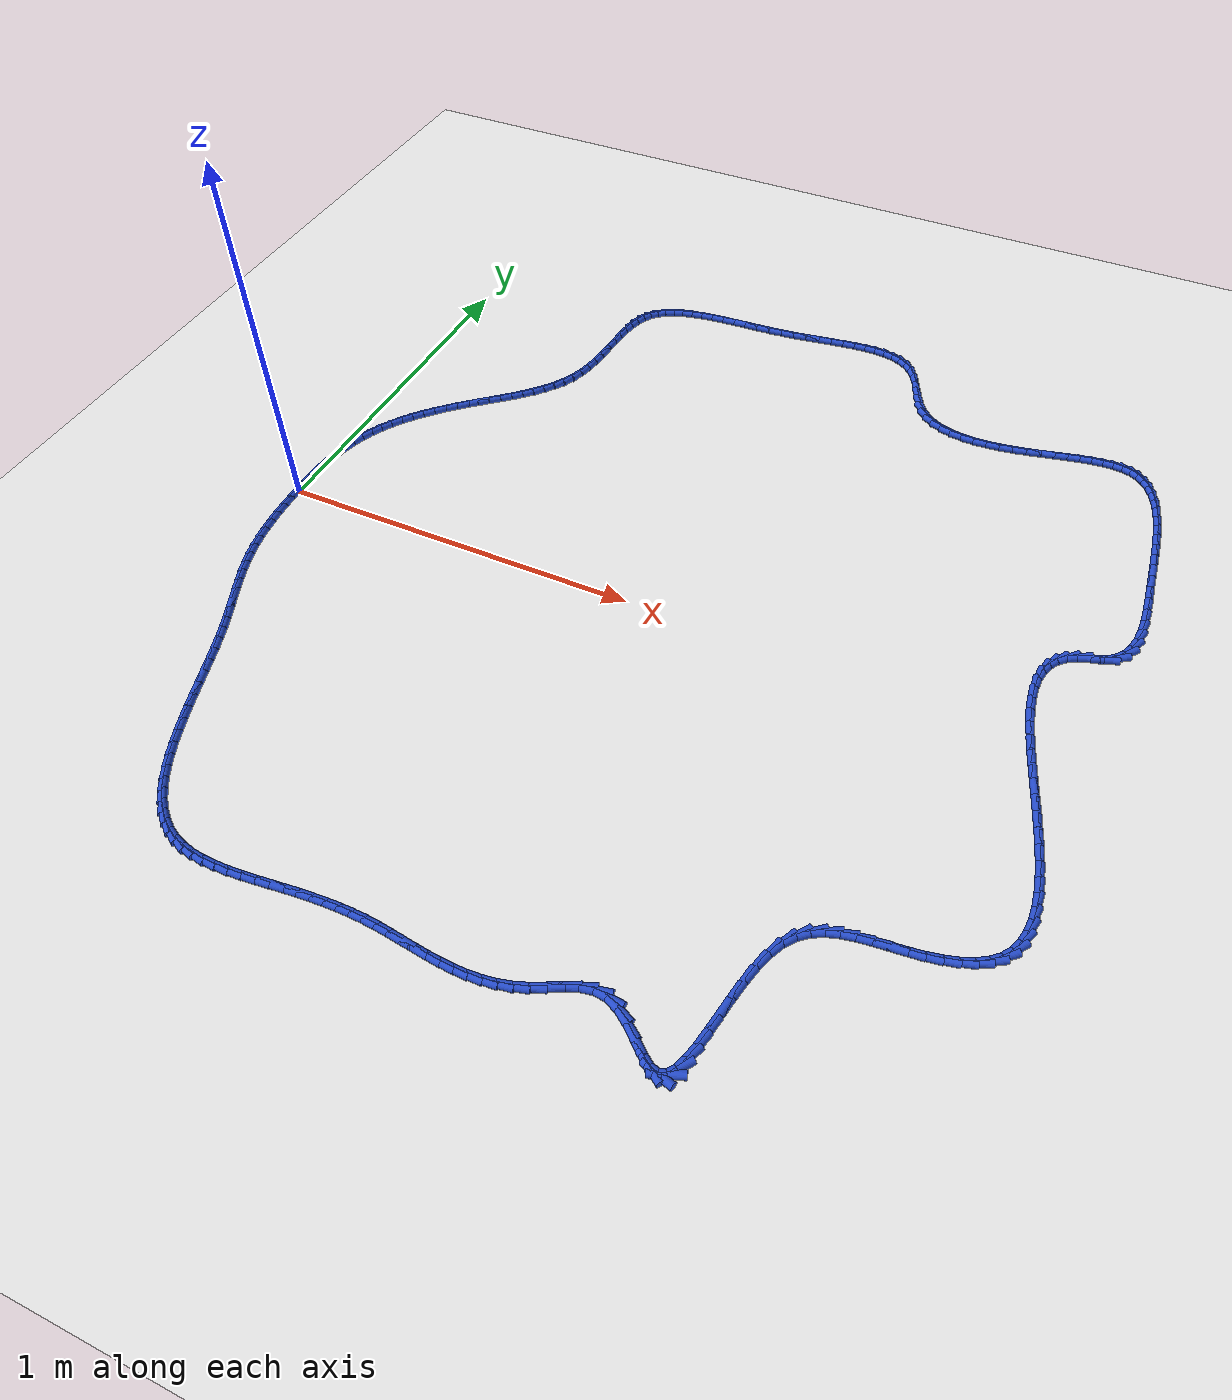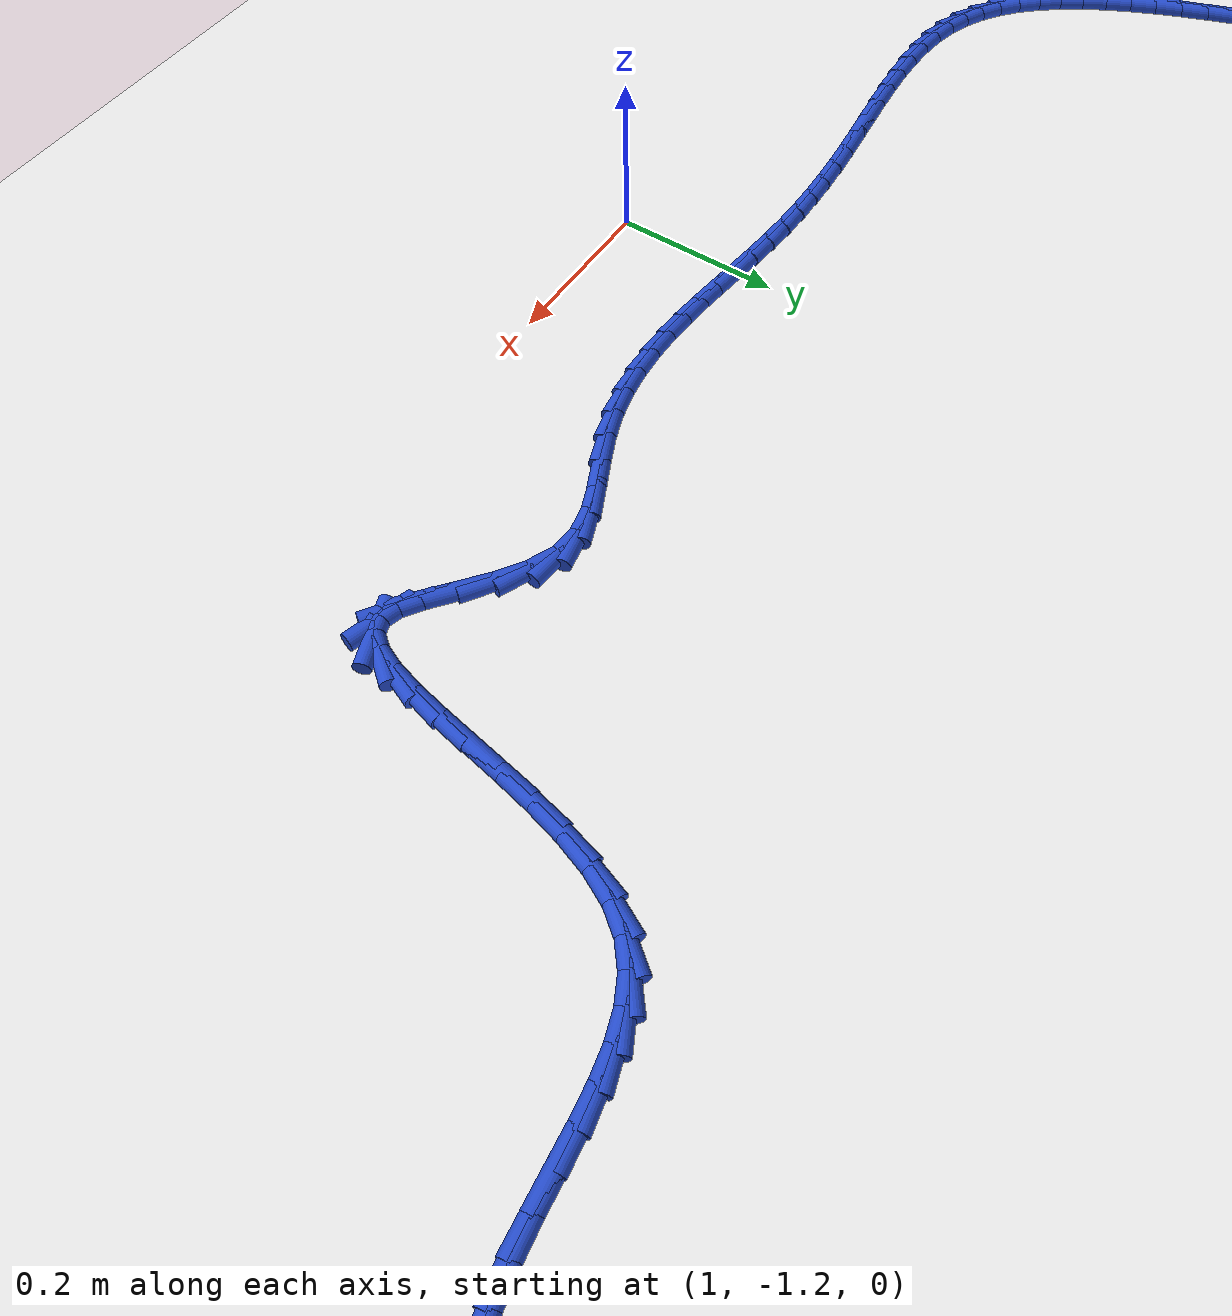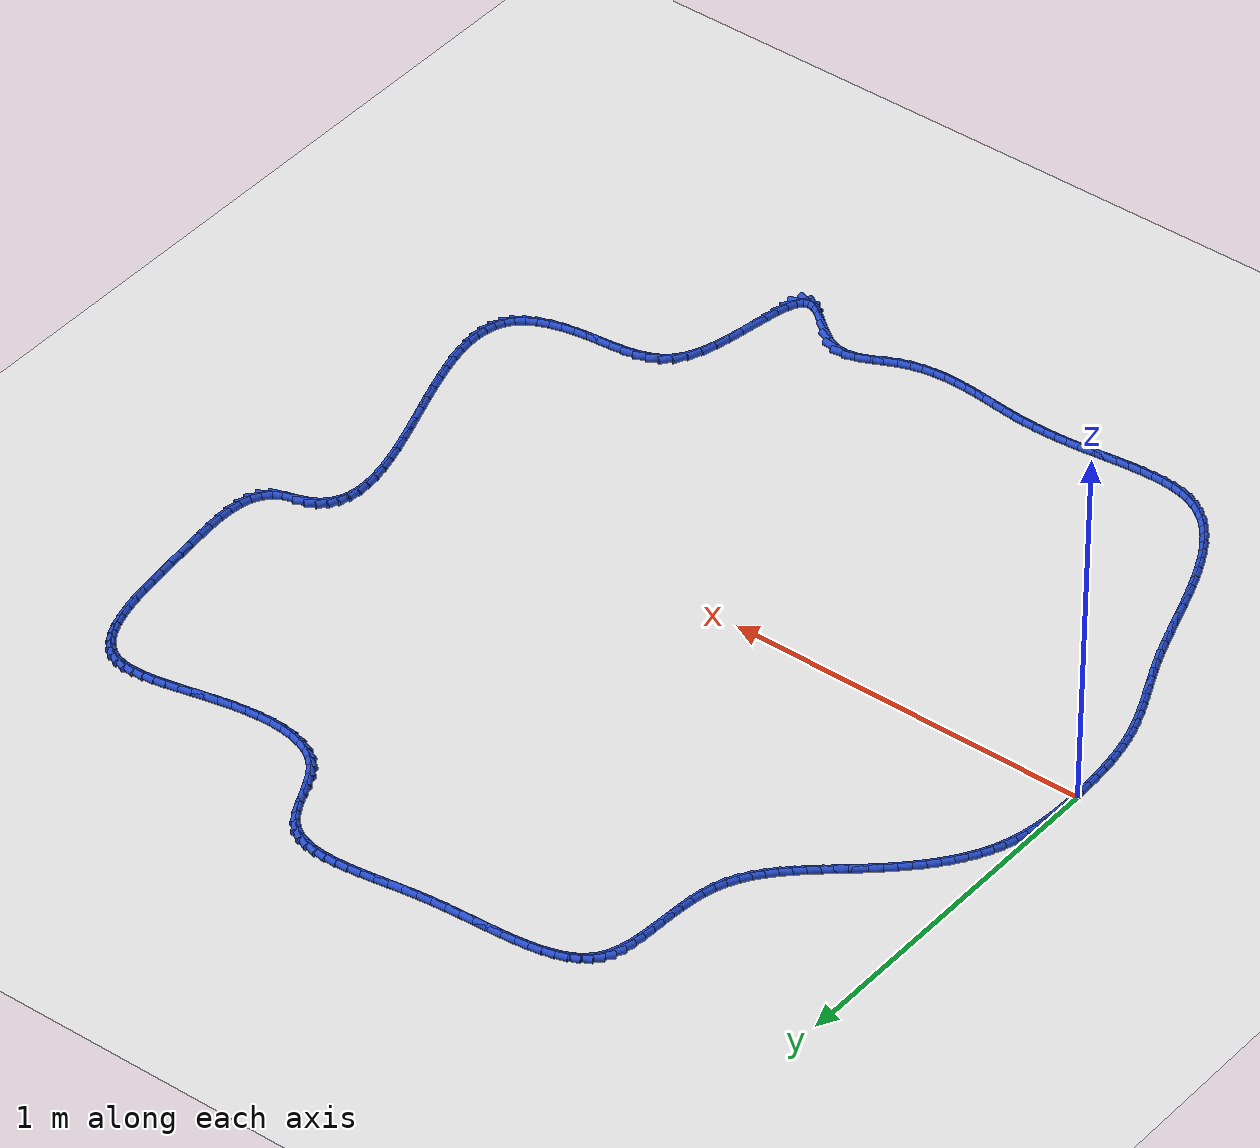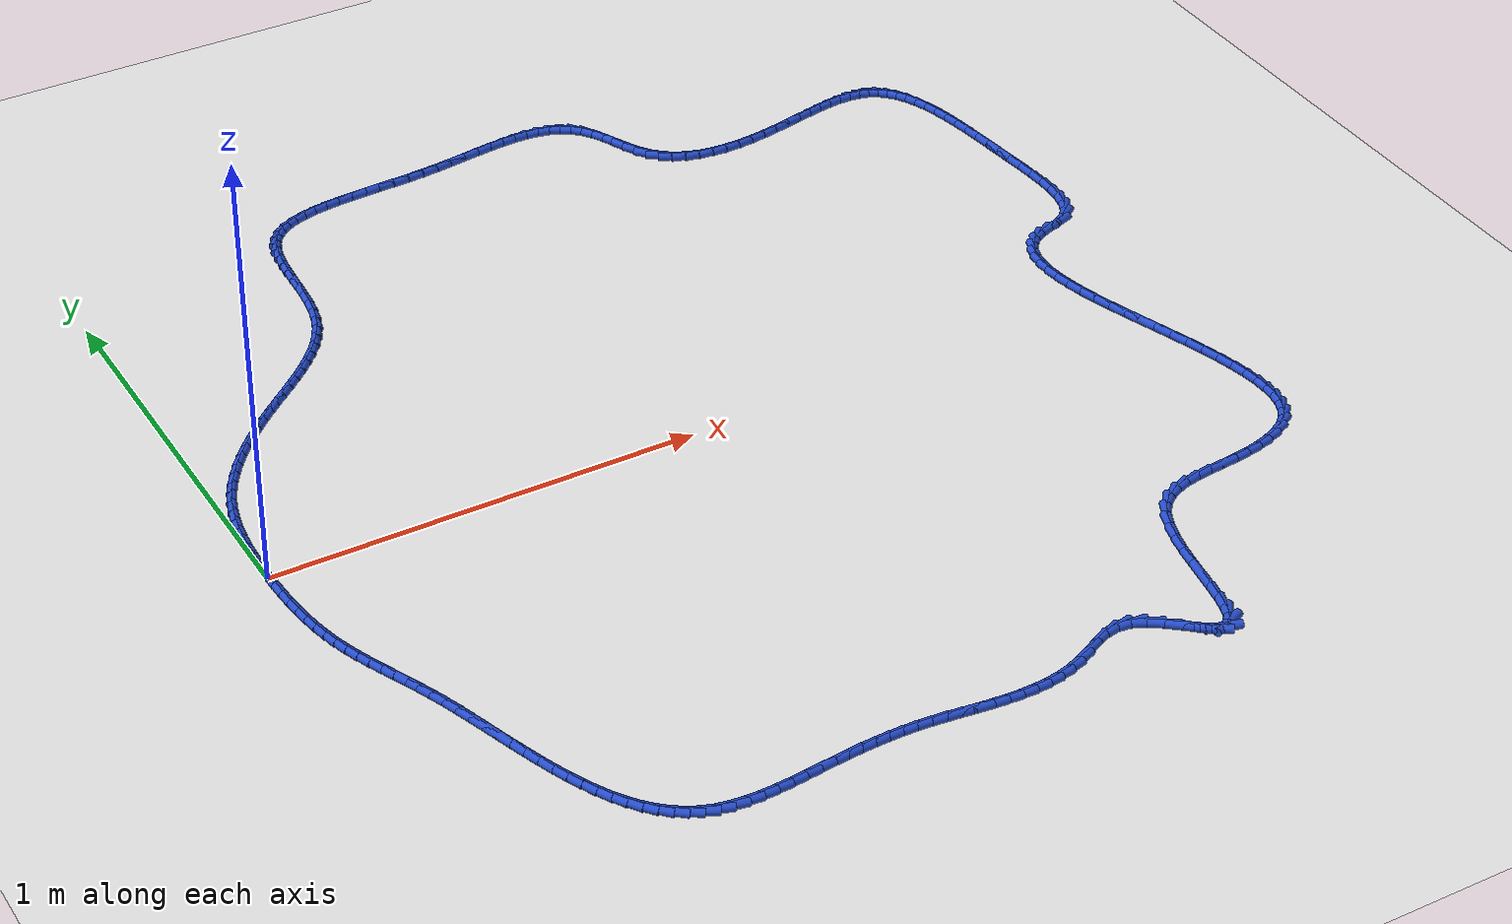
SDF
<sdf version="1.6">
 <world name="default">
  <light name="sun" type="directional">
   <pose>0 0 10 0 -0 0</pose>
   <diffuse>0.8 0.8 0.8 1</diffuse>
   <specular>0.2 0.2 0.2 1</specular>
   <attenuation>
    <range>1000</range>
    <constant>0.9</constant>
    <linear>0.01</linear>
    <quadratic>0.001</quadratic>
   </attenuation>
   <direction>-0.5 0.1 -0.9</direction>
  </light>
  <model name="ground_plane">
   <static>1</static>
   <link name="link">
    <collision name="collision">
     <geometry><plane><normal>0 0 1</normal><size>100 100</size></plane></geometry>
     <surface><friction><ode><mu>100</mu><mu2>50</mu2></ode></friction></surface>
    </collision>
    <visual name="visual">
     <cast_shadows>0</cast_shadows>
     <geometry><plane><normal>0 0 1</normal><size>100 100</size></plane></geometry>
     <material>
      <script><uri>file://media/materials/scripts/gazebo.material</uri><name>Gazebo/WhiteGlow</name></script>
     </material>
    </visual>
   </link>
  </model>
  <gravity>0 0 -9.8</gravity>
  <magnetic_field>6e-06 2.3e-05 -4.2e-05</magnetic_field>
  <atmosphere type="adiabatic"/>
  <physics name="default_physics" default="0" type="ode">
   <max_step_size>0.001</max_step_size>
   <real_time_factor>1</real_time_factor>
   <real_time_update_rate>1000</real_time_update_rate>
  </physics>
  <scene><ambient>0.4 0.4 0.4 1</ambient><background>0.7 0.7 0.7 1</background><shadows>1</shadows></scene>
  <spherical_coordinates>
   <surface_model>EARTH_WGS84</surface_model>
   <latitude_deg>0</latitude_deg>
   <longitude_deg>0</longitude_deg>
   <elevation>0</elevation>
   <heading_deg>0</heading_deg>
  </spherical_coordinates>
  <model name="line">
   <link name="link_0">
    <pose>-4.119968255444917e-18 -4.85722573273506e-17 0.01 0 1.57 -1.563860208602755</pose>
    <collision name="collision">
     <geometry><cylinder><radius>0.01</radius><length>0.08</length></cylinder></geometry>
    </collision>
    <visual name="visual">
     <material>
      <script><name>Gazebo/Blue</name><uri>file://media/materials/scripts/gazebo.material</uri></script>
     </material>
     <geometry><cylinder><radius>0.01</radius><length>0.08</length></cylinder></geometry>
    </visual>
   </link>
   <link name="link_1">
    <pose>-0.00022978712475713397 0.03312853578625313 0.01 0 1.57 1.5530690252986277</pose>
    <collision name="collision">
     <geometry><cylinder><radius>0.01</radius><length>0.08</length></cylinder></geometry>
    </collision>
    <visual name="visual">
     <material>
      <script><name>Gazebo/Blue</name><uri>file://media/materials/scripts/gazebo.material</uri></script>
     </material>
     <geometry><cylinder><radius>0.01</radius><length>0.08</length></cylinder></geometry>
    </visual>
   </link>
   <link name="link_2">
    <pose>0.0003566372274891024 0.06620536486374896 0.01 0 1.57 1.521653860908902</pose>
    <collision name="collision">
     <geometry><cylinder><radius>0.01</radius><length>0.08</length></cylinder></geometry>
    </collision>
    <visual name="visual">
     <material>
      <script><name>Gazebo/Blue</name><uri>file://media/materials/scripts/gazebo.material</uri></script>
     </material>
     <geometry><cylinder><radius>0.01</radius><length>0.08</length></cylinder></geometry>
    </visual>
   </link>
   <link name="link_3">
    <pose>0.001974363329070332 0.09909796809290748 0.01 0 1.57 1.4831003377732992</pose>
    <collision name="collision">
     <geometry><cylinder><radius>0.01</radius><length>0.08</length></cylinder></geometry>
    </collision>
    <visual name="visual">
     <material>
      <script><name>Gazebo/Blue</name><uri>file://media/materials/scripts/gazebo.material</uri></script>
     </material>
     <geometry><cylinder><radius>0.01</radius><length>0.08</length></cylinder></geometry>
    </visual>
   </link>
   <link name="link_4">
    <pose>0.00483848145231818 0.13167382633414876 0.01 0 1.57 1.4369588551673336</pose>
    <collision name="collision">
     <geometry><cylinder><radius>0.01</radius><length>0.08</length></cylinder></geometry>
    </collision>
    <visual name="visual">
     <material>
      <script><name>Gazebo/Blue</name><uri>file://media/materials/scripts/gazebo.material</uri></script>
     </material>
     <geometry><cylinder><radius>0.01</radius><length>0.08</length></cylinder></geometry>
    </visual>
   </link>
   <link name="link_5">
    <pose>0.009164081869564276 0.16380042044789275 0.01 0 1.57 1.382769461718022</pose>
    <collision name="collision">
     <geometry><cylinder><radius>0.01</radius><length>0.08</length></cylinder></geometry>
    </collision>
    <visual name="visual">
     <material>
      <script><name>Gazebo/Blue</name><uri>file://media/materials/scripts/gazebo.material</uri></script>
     </material>
     <geometry><cylinder><radius>0.01</radius><length>0.08</length></cylinder></geometry>
    </visual>
   </link>
   <link name="link_6">
    <pose>0.01516625485314025 0.19534523129455955 0.01 0 1.57 1.3201413163516609</pose>
    <collision name="collision">
     <geometry><cylinder><radius>0.01</radius><length>0.08</length></cylinder></geometry>
    </collision>
    <visual name="visual">
     <material>
      <script><name>Gazebo/Blue</name><uri>file://media/materials/scripts/gazebo.material</uri></script>
     </material>
     <geometry><cylinder><radius>0.01</radius><length>0.08</length></cylinder></geometry>
    </visual>
   </link>
   <link name="link_7">
    <pose>0.02306009067537772 0.22617573973456911 0.01 0 1.57 1.2488648858817049</pose>
    <collision name="collision">
     <geometry><cylinder><radius>0.01</radius><length>0.08</length></cylinder></geometry>
    </collision>
    <visual name="visual">
     <material>
      <script><name>Gazebo/Blue</name><uri>file://media/materials/scripts/gazebo.material</uri></script>
     </material>
     <geometry><cylinder><radius>0.01</radius><length>0.08</length></cylinder></geometry>
    </visual>
   </link>
   <link name="link_8">
    <pose>0.033060679608608326 0.25615942662834157 0.01 0 1.57 1.1708176303665927</pose>
    <collision name="collision">
     <geometry><cylinder><radius>0.01</radius><length>0.08</length></cylinder></geometry>
    </collision>
    <visual name="visual">
     <material>
      <script><name>Gazebo/Blue</name><uri>file://media/materials/scripts/gazebo.material</uri></script>
     </material>
     <geometry><cylinder><radius>0.01</radius><length>0.08</length></cylinder></geometry>
    </visual>
   </link>
   <link name="link_9">
    <pose>0.04533268314077436 0.2851871685996576 0.01 0 1.57 1.095804309412011</pose>
    <collision name="collision">
     <geometry><cylinder><radius>0.01</radius><length>0.08</length></cylinder></geometry>
    </collision>
    <visual name="visual">
     <material>
      <script><name>Gazebo/Blue</name><uri>file://media/materials/scripts/gazebo.material</uri></script>
     </material>
     <geometry><cylinder><radius>0.01</radius><length>0.08</length></cylinder></geometry>
    </visual>
   </link>
   <link name="link_10">
    <pose>0.059775994024964425 0.31327267820302707 0.01 0 1.57 1.0274184675150033</pose>
    <collision name="collision">
     <geometry><cylinder><radius>0.01</radius><length>0.08</length></cylinder></geometry>
    </collision>
    <visual name="visual">
     <material>
      <script><name>Gazebo/Blue</name><uri>file://media/materials/scripts/gazebo.material</uri></script>
     </material>
     <geometry><cylinder><radius>0.01</radius><length>0.08</length></cylinder></geometry>
    </visual>
   </link>
   <link name="link_11">
    <pose>0.0762039113784414 0.3404698419578265 0.01 0 1.57 0.9659018627370537</pose>
    <collision name="collision">
     <geometry><cylinder><radius>0.01</radius><length>0.08</length></cylinder></geometry>
    </collision>
    <visual name="visual">
     <material>
      <script><name>Gazebo/Blue</name><uri>file://media/materials/scripts/gazebo.material</uri></script>
     </material>
     <geometry><cylinder><radius>0.01</radius><length>0.08</length></cylinder></geometry>
    </visual>
   </link>
   <link name="link_12">
    <pose>0.09442968509827855 0.3668325692184842 0.01 0 1.57 0.9112256142074939</pose>
    <collision name="collision">
     <geometry><cylinder><radius>0.01</radius><length>0.08</length></cylinder></geometry>
    </collision>
    <visual name="visual">
     <material>
      <script><name>Gazebo/Blue</name><uri>file://media/materials/scripts/gazebo.material</uri></script>
     </material>
     <geometry><cylinder><radius>0.01</radius><length>0.08</length></cylinder></geometry>
    </visual>
   </link>
   <link name="link_13">
    <pose>0.11426656508154909 0.39241476933942865 0.01 0 1.57 0.8631809461934924</pose>
    <collision name="collision">
     <geometry><cylinder><radius>0.01</radius><length>0.08</length></cylinder></geometry>
    </collision>
    <visual name="visual">
     <material>
      <script><name>Gazebo/Blue</name><uri>file://media/materials/scripts/gazebo.material</uri></script>
     </material>
     <geometry><cylinder><radius>0.01</radius><length>0.08</length></cylinder></geometry>
    </visual>
   </link>
   <link name="link_14">
    <pose>0.13552780122532632 0.4172703516750884 0.01 0 1.57 0.8214572864836346</pose>
    <collision name="collision">
     <geometry><cylinder><radius>0.01</radius><length>0.08</length></cylinder></geometry>
    </collision>
    <visual name="visual">
     <material>
      <script><name>Gazebo/Blue</name><uri>file://media/materials/scripts/gazebo.material</uri></script>
     </material>
     <geometry><cylinder><radius>0.01</radius><length>0.08</length></cylinder></geometry>
    </visual>
   </link>
   <link name="link_15">
    <pose>0.1580266434266834 0.4414532255798916 0.01 0 1.57 0.7857033113617928</pose>
    <collision name="collision">
     <geometry><cylinder><radius>0.01</radius><length>0.08</length></cylinder></geometry>
    </collision>
    <visual name="visual">
     <material>
      <script><name>Gazebo/Blue</name><uri>file://media/materials/scripts/gazebo.material</uri></script>
     </material>
     <geometry><cylinder><radius>0.01</radius><length>0.08</length></cylinder></geometry>
    </visual>
   </link>
   <link name="link_16">
    <pose>0.1815763415826937 0.4650173004082669 0.01 0 1.57 0.7555709073965531</pose>
    <collision name="collision">
     <geometry><cylinder><radius>0.01</radius><length>0.08</length></cylinder></geometry>
    </collision>
    <visual name="visual">
     <material>
      <script><name>Gazebo/Blue</name><uri>file://media/materials/scripts/gazebo.material</uri></script>
     </material>
     <geometry><cylinder><radius>0.01</radius><length>0.08</length></cylinder></geometry>
    </visual>
   </link>
   <link name="link_17">
    <pose>0.20599014559043044 0.48801648551464266 0.01 0 1.57 0.7307449985027238</pose>
    <collision name="collision">
     <geometry><cylinder><radius>0.01</radius><length>0.08</length></cylinder></geometry>
    </collision>
    <visual name="visual">
     <material>
      <script><name>Gazebo/Blue</name><uri>file://media/materials/scripts/gazebo.material</uri></script>
     </material>
     <geometry><cylinder><radius>0.01</radius><length>0.08</length></cylinder></geometry>
    </visual>
   </link>
   <link name="link_18">
    <pose>0.23108130534696675 0.5105046902534471 0.01 0 1.57 0.7116961287206145</pose>
    <collision name="collision">
     <geometry><cylinder><radius>0.01</radius><length>0.08</length></cylinder></geometry>
    </collision>
    <visual name="visual">
     <material>
      <script><name>Gazebo/Blue</name><uri>file://media/materials/scripts/gazebo.material</uri></script>
     </material>
     <geometry><cylinder><radius>0.01</radius><length>0.08</length></cylinder></geometry>
    </visual>
   </link>
   <link name="link_19">
    <pose>0.2566465327931422 0.5325542434749874 0.01 0 1.57 0.7029988984063777</pose>
    <collision name="collision">
     <geometry><cylinder><radius>0.01</radius><length>0.08</length></cylinder></geometry>
    </collision>
    <visual name="visual">
     <material>
      <script><name>Gazebo/Blue</name><uri>file://media/materials/scripts/gazebo.material</uri></script>
     </material>
     <geometry><cylinder><radius>0.01</radius><length>0.08</length></cylinder></geometry>
    </visual>
   </link>
   <link name="link_20">
    <pose>0.2823749927854412 0.5543572568521266 0.01 0 1.57 0.7065207644994871</pose>
    <collision name="collision">
     <geometry><cylinder><radius>0.01</radius><length>0.08</length></cylinder></geometry>
    </collision>
    <visual name="visual">
     <material>
      <script><name>Gazebo/Blue</name><uri>file://media/materials/scripts/gazebo.material</uri></script>
     </material>
     <geometry><cylinder><radius>0.01</radius><length>0.08</length></cylinder></geometry>
    </visual>
   </link>
   <link name="link_21">
    <pose>0.3079128461987999 0.5761537386448085 0.01 0 1.57 0.7224657098544726</pose>
    <collision name="collision">
     <geometry><cylinder><radius>0.01</radius><length>0.08</length></cylinder></geometry>
    </collision>
    <visual name="visual">
     <material>
      <script><name>Gazebo/Blue</name><uri>file://media/materials/scripts/gazebo.material</uri></script>
     </material>
     <geometry><cylinder><radius>0.01</radius><length>0.08</length></cylinder></geometry>
    </visual>
   </link>
   <link name="link_22">
    <pose>0.33290614052575945 0.5981838233949993 0.01 0 1.57 0.7512696150963581</pose>
    <collision name="collision">
     <geometry><cylinder><radius>0.01</radius><length>0.08</length></cylinder></geometry>
    </collision>
    <visual name="visual">
     <material>
      <script><name>Gazebo/Blue</name><uri>file://media/materials/scripts/gazebo.material</uri></script>
     </material>
     <geometry><cylinder><radius>0.01</radius><length>0.08</length></cylinder></geometry>
    </visual>
   </link>
   <link name="link_23">
    <pose>0.35700092325886096 0.6206876456446644 0.01 0 1.57 0.7935476910527351</pose>
    <collision name="collision">
     <geometry><cylinder><radius>0.01</radius><length>0.08</length></cylinder></geometry>
    </collision>
    <visual name="visual">
     <material>
      <script><name>Gazebo/Blue</name><uri>file://media/materials/scripts/gazebo.material</uri></script>
     </material>
     <geometry><cylinder><radius>0.01</radius><length>0.08</length></cylinder></geometry>
    </visual>
   </link>
   <link name="link_24">
    <pose>0.3798432418906455 0.6439053399357703 0.01 0 1.57 0.8499626452688942</pose>
    <collision name="collision">
     <geometry><cylinder><radius>0.01</radius><length>0.08</length></cylinder></geometry>
    </collision>
    <visual name="visual">
     <material>
      <script><name>Gazebo/Blue</name><uri>file://media/materials/scripts/gazebo.material</uri></script>
     </material>
     <geometry><cylinder><radius>0.01</radius><length>0.08</length></cylinder></geometry>
    </visual>
   </link>
   <link name="link_25">
    <pose>0.40107914391365423 0.6680770408102826 0.01 0 1.57 0.9209885288301519</pose>
    <collision name="collision">
     <geometry><cylinder><radius>0.01</radius><length>0.08</length></cylinder></geometry>
    </collision>
    <visual name="visual">
     <material>
      <script><name>Gazebo/Blue</name><uri>file://media/materials/scripts/gazebo.material</uri></script>
     </material>
     <geometry><cylinder><radius>0.01</radius><length>0.08</length></cylinder></geometry>
    </visual>
   </link>
   <link name="link_26">
    <pose>0.4203546768204281 0.6934428828101674 0.01 0 1.57 1.0065518093062245</pose>
    <collision name="collision">
     <geometry><cylinder><radius>0.01</radius><length>0.08</length></cylinder></geometry>
    </collision>
    <visual name="visual">
     <material>
      <script><name>Gazebo/Blue</name><uri>file://media/materials/scripts/gazebo.material</uri></script>
     </material>
     <geometry><cylinder><radius>0.01</radius><length>0.08</length></cylinder></geometry>
    </visual>
   </link>
   <link name="link_27">
    <pose>0.4373158881035083 0.7202430004773905 0.01 0 1.57 1.1055857865491392</pose>
    <collision name="collision">
     <geometry><cylinder><radius>0.01</radius><length>0.08</length></cylinder></geometry>
    </collision>
    <visual name="visual">
     <material>
      <script><name>Gazebo/Blue</name><uri>file://media/materials/scripts/gazebo.material</uri></script>
     </material>
     <geometry><cylinder><radius>0.01</radius><length>0.08</length></cylinder></geometry>
    </visual>
   </link>
   <link name="link_28">
    <pose>0.45160882525543605 0.7487175283539182 0.01 0 1.57 1.2156180117135698</pose>
    <collision name="collision">
     <geometry><cylinder><radius>0.01</radius><length>0.08</length></cylinder></geometry>
    </collision>
    <visual name="visual">
     <material>
      <script><name>Gazebo/Blue</name><uri>file://media/materials/scripts/gazebo.material</uri></script>
     </material>
     <geometry><cylinder><radius>0.01</radius><length>0.08</length></cylinder></geometry>
    </visual>
   </link>
   <link name="link_29">
    <pose>0.4628801880739714 0.7791060988051834 0.01 0 1.57 1.3236279337653039</pose>
    <collision name="collision">
     <geometry><cylinder><radius>0.01</radius><length>0.08</length></cylinder></geometry>
    </collision>
    <visual name="visual">
     <material>
      <script><name>Gazebo/Blue</name><uri>file://media/materials/scripts/gazebo.material</uri></script>
     </material>
     <geometry><cylinder><radius>0.01</radius><length>0.08</length></cylinder></geometry>
    </visual>
   </link>
   <link name="link_30">
    <pose>0.4710402944478253 0.8114453980678558 0.01 0 1.57 1.4059331654023732</pose>
    <collision name="collision">
     <geometry><cylinder><radius>0.01</radius><length>0.08</length></cylinder></geometry>
    </collision>
    <visual name="visual">
     <material>
      <script><name>Gazebo/Blue</name><uri>file://media/materials/scripts/gazebo.material</uri></script>
     </material>
     <geometry><cylinder><radius>0.01</radius><length>0.08</length></cylinder></geometry>
    </visual>
   </link>
   <link name="link_31">
    <pose>0.47666597273250555 0.8452589999494537 0.01 0 1.57 1.4626216940751016</pose>
    <collision name="collision">
     <geometry><cylinder><radius>0.01</radius><length>0.08</length></cylinder></geometry>
    </collision>
    <visual name="visual">
     <material>
      <script><name>Gazebo/Blue</name><uri>file://media/materials/scripts/gazebo.material</uri></script>
     </material>
     <geometry><cylinder><radius>0.01</radius><length>0.08</length></cylinder></geometry>
    </visual>
   </link>
   <link name="link_32">
    <pose>0.48043777723819026 0.8799906249330267 0.01 0 1.57 1.4968863020705354</pose>
    <collision name="collision">
     <geometry><cylinder><radius>0.01</radius><length>0.08</length></cylinder></geometry>
    </collision>
    <visual name="visual">
     <material>
      <script><name>Gazebo/Blue</name><uri>file://media/materials/scripts/gazebo.material</uri></script>
     </material>
     <geometry><cylinder><radius>0.01</radius><length>0.08</length></cylinder></geometry>
    </visual>
   </link>
   <link name="link_33">
    <pose>0.4830362622750574 0.9150839935016243 0.01 0 1.57 1.5105315589571833</pose>
    <collision name="collision">
     <geometry><cylinder><radius>0.01</radius><length>0.08</length></cylinder></geometry>
    </collision>
    <visual name="visual">
     <material>
      <script><name>Gazebo/Blue</name><uri>file://media/materials/scripts/gazebo.material</uri></script>
     </material>
     <geometry><cylinder><radius>0.01</radius><length>0.08</length></cylinder></geometry>
    </visual>
   </link>
   <link name="link_34">
    <pose>0.48514198215328497 0.9499828261382951 0.01 0 1.57 1.5037332914445531</pose>
    <collision name="collision">
     <geometry><cylinder><radius>0.01</radius><length>0.08</length></cylinder></geometry>
    </collision>
    <visual name="visual">
     <material>
      <script><name>Gazebo/Blue</name><uri>file://media/materials/scripts/gazebo.material</uri></script>
     </material>
     <geometry><cylinder><radius>0.01</radius><length>0.08</length></cylinder></geometry>
    </visual>
   </link>
   <link name="link_35">
    <pose>0.487435491183051 0.9841308433260892 0.01 0 1.57 1.4748143401871472</pose>
    <collision name="collision">
     <geometry><cylinder><radius>0.01</radius><length>0.08</length></cylinder></geometry>
    </collision>
    <visual name="visual">
     <material>
      <script><name>Gazebo/Blue</name><uri>file://media/materials/scripts/gazebo.material</uri></script>
     </material>
     <geometry><cylinder><radius>0.01</radius><length>0.08</length></cylinder></geometry>
    </visual>
   </link>
   <link name="link_36">
    <pose>0.4905973436745334 1.0169717655480552 0.01 0 1.57 1.419882717696217</pose>
    <collision name="collision">
     <geometry><cylinder><radius>0.01</radius><length>0.08</length></cylinder></geometry>
    </collision>
    <visual name="visual">
     <material>
      <script><name>Gazebo/Blue</name><uri>file://media/materials/scripts/gazebo.material</uri></script>
     </material>
     <geometry><cylinder><radius>0.01</radius><length>0.08</length></cylinder></geometry>
    </visual>
   </link>
   <link name="link_37">
    <pose>0.4953080939379103 1.0479493132872433 0.01 0 1.57 1.3323957041869539</pose>
    <collision name="collision">
     <geometry><cylinder><radius>0.01</radius><length>0.08</length></cylinder></geometry>
    </collision>
    <visual name="visual">
     <material>
      <script><name>Gazebo/Blue</name><uri>file://media/materials/scripts/gazebo.material</uri></script>
     </material>
     <geometry><cylinder><radius>0.01</radius><length>0.08</length></cylinder></geometry>
    </visual>
   </link>
   <link name="link_38">
    <pose>0.5022482962833598 1.0765072070267023 0.01 0 1.57 1.2032481967909927</pose>
    <collision name="collision">
     <geometry><cylinder><radius>0.01</radius><length>0.08</length></cylinder></geometry>
    </collision>
    <visual name="visual">
     <material>
      <script><name>Gazebo/Blue</name><uri>file://media/materials/scripts/gazebo.material</uri></script>
     </material>
     <geometry><cylinder><radius>0.01</radius><length>0.08</length></cylinder></geometry>
    </visual>
   </link>
   <link name="link_39">
    <pose>0.5120985050210598 1.1020891672494812 0.01 0 1.57 1.0242404055056542</pose>
    <collision name="collision">
     <geometry><cylinder><radius>0.01</radius><length>0.08</length></cylinder></geometry>
    </collision>
    <visual name="visual">
     <material>
      <script><name>Gazebo/Blue</name><uri>file://media/materials/scripts/gazebo.material</uri></script>
     </material>
     <geometry><cylinder><radius>0.01</radius><length>0.08</length></cylinder></geometry>
    </visual>
   </link>
   <link name="link_40">
    <pose>0.5255225985327883 1.1241546053162494 0.01 0 1.57 0.8195457834675507</pose>
    <collision name="collision">
     <geometry><cylinder><radius>0.01</radius><length>0.08</length></cylinder></geometry>
    </collision>
    <visual name="visual">
     <material>
      <script><name>Gazebo/Blue</name><uri>file://media/materials/scripts/gazebo.material</uri></script>
     </material>
     <geometry><cylinder><radius>0.01</radius><length>0.08</length></cylinder></geometry>
    </visual>
   </link>
   <link name="link_41">
    <pose>0.5427356243029462 1.1425852509446088 0.01 0 1.57 0.6307433806824019</pose>
    <collision name="collision">
     <geometry><cylinder><radius>0.01</radius><length>0.08</length></cylinder></geometry>
    </collision>
    <visual name="visual">
     <material>
      <script><name>Gazebo/Blue</name><uri>file://media/materials/scripts/gazebo.material</uri></script>
     </material>
     <geometry><cylinder><radius>0.01</radius><length>0.08</length></cylinder></geometry>
    </visual>
   </link>
   <link name="link_42">
    <pose>0.5634642224468274 1.1577223908898824 0.01 0 1.57 0.471466870205109</pose>
    <collision name="collision">
     <geometry><cylinder><radius>0.01</radius><length>0.08</length></cylinder></geometry>
    </collision>
    <visual name="visual">
     <material>
      <script><name>Gazebo/Blue</name><uri>file://media/materials/scripts/gazebo.material</uri></script>
     </material>
     <geometry><cylinder><radius>0.01</radius><length>0.08</length></cylinder></geometry>
    </visual>
   </link>
   <link name="link_43">
    <pose>0.5874104241342258 1.1699304671970359 0.01 0 1.57 0.3446245084557042</pose>
    <collision name="collision">
     <geometry><cylinder><radius>0.01</radius><length>0.08</length></cylinder></geometry>
    </collision>
    <visual name="visual">
     <material>
      <script><name>Gazebo/Blue</name><uri>file://media/materials/scripts/gazebo.material</uri></script>
     </material>
     <geometry><cylinder><radius>0.01</radius><length>0.08</length></cylinder></geometry>
    </visual>
   </link>
   <link name="link_44">
    <pose>0.614276260534935 1.1795739219110366 0.01 0 1.57 0.24725628020326823</pose>
    <collision name="collision">
     <geometry><cylinder><radius>0.01</radius><length>0.08</length></cylinder></geometry>
    </collision>
    <visual name="visual">
     <material>
      <script><name>Gazebo/Blue</name><uri>file://media/materials/scripts/gazebo.material</uri></script>
     </material>
     <geometry><cylinder><radius>0.01</radius><length>0.08</length></cylinder></geometry>
    </visual>
   </link>
   <link name="link_45">
    <pose>0.6437637628187494 1.1870171970768506 0.01 0 1.57 0.1744830754683009</pose>
    <collision name="collision">
     <geometry><cylinder><radius>0.01</radius><length>0.08</length></cylinder></geometry>
    </collision>
    <visual name="visual">
     <material>
      <script><name>Gazebo/Blue</name><uri>file://media/materials/scripts/gazebo.material</uri></script>
     </material>
     <geometry><cylinder><radius>0.01</radius><length>0.08</length></cylinder></geometry>
    </visual>
   </link>
   <link name="link_46">
    <pose>0.6755749621554622 1.1926247347394436 0.01 0 1.57 0.12163701046163239</pose>
    <collision name="collision">
     <geometry><cylinder><radius>0.01</radius><length>0.08</length></cylinder></geometry>
    </collision>
    <visual name="visual">
     <material>
      <script><name>Gazebo/Blue</name><uri>file://media/materials/scripts/gazebo.material</uri></script>
     </material>
     <geometry><cylinder><radius>0.01</radius><length>0.08</length></cylinder></geometry>
    </visual>
   </link>
   <link name="link_47">
    <pose>0.7094118897148673 1.1967609769437817 0.01 0 1.57 0.08497456677011156</pose>
    <collision name="collision">
     <geometry><cylinder><radius>0.01</radius><length>0.08</length></cylinder></geometry>
    </collision>
    <visual name="visual">
     <material>
      <script><name>Gazebo/Blue</name><uri>file://media/materials/scripts/gazebo.material</uri></script>
     </material>
     <geometry><cylinder><radius>0.01</radius><length>0.08</length></cylinder></geometry>
    </visual>
   </link>
   <link name="link_48">
    <pose>0.744976576666759 1.1997903657348314 0.01 0 1.57 0.0617408570744163</pose>
    <collision name="collision">
     <geometry><cylinder><radius>0.01</radius><length>0.08</length></cylinder></geometry>
    </collision>
    <visual name="visual">
     <material>
      <script><name>Gazebo/Blue</name><uri>file://media/materials/scripts/gazebo.material</uri></script>
     </material>
     <geometry><cylinder><radius>0.01</radius><length>0.08</length></cylinder></geometry>
    </visual>
   </link>
   <link name="link_49">
    <pose>0.7819710541809302 1.202077343157559 0.01 0 1.57 0.05002885657419668</pose>
    <collision name="collision">
     <geometry><cylinder><radius>0.01</radius><length>0.08</length></cylinder></geometry>
    </collision>
    <visual name="visual">
     <material>
      <script><name>Gazebo/Blue</name><uri>file://media/materials/scripts/gazebo.material</uri></script>
     </material>
     <geometry><cylinder><radius>0.01</radius><length>0.08</length></cylinder></geometry>
    </visual>
   </link>
   <link name="link_50">
    <pose>0.8200973534271754 1.2039863512569309 0.01 0 1.57 0.04861345002937244</pose>
    <collision name="collision">
     <geometry><cylinder><radius>0.01</radius><length>0.08</length></cylinder></geometry>
    </collision>
    <visual name="visual">
     <material>
      <script><name>Gazebo/Blue</name><uri>file://media/materials/scripts/gazebo.material</uri></script>
     </material>
     <geometry><cylinder><radius>0.01</radius><length>0.08</length></cylinder></geometry>
    </visual>
   </link>
   <link name="link_51">
    <pose>0.8590575055752883 1.2058818320779132 0.01 0 1.57 0.05681527006630187</pose>
    <collision name="collision">
     <geometry><cylinder><radius>0.01</radius><length>0.08</length></cylinder></geometry>
    </collision>
    <visual name="visual">
     <material>
      <script><name>Gazebo/Blue</name><uri>file://media/materials/scripts/gazebo.material</uri></script>
     </material>
     <geometry><cylinder><radius>0.01</radius><length>0.08</length></cylinder></geometry>
    </visual>
   </link>
   <link name="link_52">
    <pose>0.8985535417950622 1.2081282276654715 0.01 0 1.57 0.07440199604239602</pose>
    <collision name="collision">
     <geometry><cylinder><radius>0.01</radius><length>0.08</length></cylinder></geometry>
    </collision>
    <visual name="visual">
     <material>
      <script><name>Gazebo/Blue</name><uri>file://media/materials/scripts/gazebo.material</uri></script>
     </material>
     <geometry><cylinder><radius>0.01</radius><length>0.08</length></cylinder></geometry>
    </visual>
   </link>
   <link name="link_53">
    <pose>0.938287493256291 1.211089980064572 0.01 0 1.57 0.10117800617957905</pose>
    <collision name="collision">
     <geometry><cylinder><radius>0.01</radius><length>0.08</length></cylinder></geometry>
    </collision>
    <visual name="visual">
     <material>
      <script><name>Gazebo/Blue</name><uri>file://media/materials/scripts/gazebo.material</uri></script>
     </material>
     <geometry><cylinder><radius>0.01</radius><length>0.08</length></cylinder></geometry>
    </visual>
   </link>
   <link name="link_54">
    <pose>0.9779623935951675 1.2151179615664336 0.01 0 1.57 0.12746172641254064</pose>
    <collision name="collision">
     <geometry><cylinder><radius>0.01</radius><length>0.08</length></cylinder></geometry>
    </collision>
    <visual name="visual">
     <material>
      <script><name>Gazebo/Blue</name><uri>file://media/materials/scripts/gazebo.material</uri></script>
     </material>
     <geometry><cylinder><radius>0.01</radius><length>0.08</length></cylinder></geometry>
    </visual>
   </link>
   <link name="link_55">
    <pose>1.0173109966244924 1.220160741224134 0.01 0 1.57 0.14202264424913053</pose>
    <collision name="collision">
     <geometry><cylinder><radius>0.01</radius><length>0.08</length></cylinder></geometry>
    </collision>
    <visual name="visual">
     <material>
      <script><name>Gazebo/Blue</name><uri>file://media/materials/scripts/gazebo.material</uri></script>
     </material>
     <geometry><cylinder><radius>0.01</radius><length>0.08</length></cylinder></geometry>
    </visual>
   </link>
   <link name="link_56">
    <pose>1.0561000302153936 1.225707002745677 0.01 0 1.57 0.14408815502588676</pose>
    <collision name="collision">
     <geometry><cylinder><radius>0.01</radius><length>0.08</length></cylinder></geometry>
    </collision>
    <visual name="visual">
     <material>
      <script><name>Gazebo/Blue</name><uri>file://media/materials/scripts/gazebo.material</uri></script>
     </material>
     <geometry><cylinder><radius>0.01</radius><length>0.08</length></cylinder></geometry>
    </visual>
   </link>
   <link name="link_57">
    <pose>1.0940980802571028 1.2312202790228168 0.01 0 1.57 0.13291653833087252</pose>
    <collision name="collision">
     <geometry><cylinder><radius>0.01</radius><length>0.08</length></cylinder></geometry>
    </collision>
    <visual name="visual">
     <material>
      <script><name>Gazebo/Blue</name><uri>file://media/materials/scripts/gazebo.material</uri></script>
     </material>
     <geometry><cylinder><radius>0.01</radius><length>0.08</length></cylinder></geometry>
    </visual>
   </link>
   <link name="link_58">
    <pose>1.1310737326388538 1.2361641029473067 0.01 0 1.57 0.10702804761849119</pose>
    <collision name="collision">
     <geometry><cylinder><radius>0.01</radius><length>0.08</length></cylinder></geometry>
    </collision>
    <visual name="visual">
     <material>
      <script><name>Gazebo/Blue</name><uri>file://media/materials/scripts/gazebo.material</uri></script>
     </material>
     <geometry><cylinder><radius>0.01</radius><length>0.08</length></cylinder></geometry>
    </visual>
   </link>
   <link name="link_59">
    <pose>1.1667955732498794 1.2400020074109002 0.01 0 1.57 0.06404008459849984</pose>
    <collision name="collision">
     <geometry><cylinder><radius>0.01</radius><length>0.08</length></cylinder></geometry>
    </collision>
    <visual name="visual">
     <material>
      <script><name>Gazebo/Blue</name><uri>file://media/materials/scripts/gazebo.material</uri></script>
     </material>
     <geometry><cylinder><radius>0.01</radius><length>0.08</length></cylinder></geometry>
    </visual>
   </link>
   <link name="link_60">
    <pose>1.201032187979413 1.2421975253053505 0.01 0 1.57 0.0005124301521370102</pose>
    <collision name="collision">
     <geometry><cylinder><radius>0.01</radius><length>0.08</length></cylinder></geometry>
    </collision>
    <visual name="visual">
     <material>
      <script><name>Gazebo/Blue</name><uri>file://media/materials/scripts/gazebo.material</uri></script>
     </material>
     <geometry><cylinder><radius>0.01</radius><length>0.08</length></cylinder></geometry>
    </visual>
   </link>
   <link name="link_61">
    <pose>1.233552162716687 1.2422141895224112 0.01 0 1.57 -0.08804418489723281</pose>
    <collision name="collision">
     <geometry><cylinder><radius>0.01</radius><length>0.08</length></cylinder></geometry>
    </collision>
    <visual name="visual">
     <material>
      <script><name>Gazebo/Blue</name><uri>file://media/materials/scripts/gazebo.material</uri></script>
     </material>
     <geometry><cylinder><radius>0.01</radius><length>0.08</length></cylinder></geometry>
    </visual>
   </link>
   <link name="link_62">
    <pose>1.2641240833509346 1.239515532953836 0.01 0 1.57 -0.20658835754524088</pose>
    <collision name="collision">
     <geometry><cylinder><radius>0.01</radius><length>0.08</length></cylinder></geometry>
    </collision>
    <visual name="visual">
     <material>
      <script><name>Gazebo/Blue</name><uri>file://media/materials/scripts/gazebo.material</uri></script>
     </material>
     <geometry><cylinder><radius>0.01</radius><length>0.08</length></cylinder></geometry>
    </visual>
   </link>
   <link name="link_63">
    <pose>1.2925165357713895 1.2335650884913778 0.01 0 1.57 -0.35862255043536795</pose>
    <collision name="collision">
     <geometry><cylinder><radius>0.01</radius><length>0.08</length></cylinder></geometry>
    </collision>
    <visual name="visual">
     <material>
      <script><name>Gazebo/Blue</name><uri>file://media/materials/scripts/gazebo.material</uri></script>
     </material>
     <geometry><cylinder><radius>0.01</radius><length>0.08</length></cylinder></geometry>
    </visual>
   </link>
   <link name="link_64">
    <pose>1.3184981058672838 1.2238263890267904 0.01 0 1.57 -0.5423031485891293</pose>
    <collision name="collision">
     <geometry><cylinder><radius>0.01</radius><length>0.08</length></cylinder></geometry>
    </collision>
    <visual name="visual">
     <material>
      <script><name>Gazebo/Blue</name><uri>file://media/materials/scripts/gazebo.material</uri></script>
     </material>
     <geometry><cylinder><radius>0.01</radius><length>0.08</length></cylinder></geometry>
    </visual>
   </link>
   <link name="link_65">
    <pose>1.3418373795278513 1.2097629674518275 0.01 0 1.57 -0.7462978801994674</pose>
    <collision name="collision">
     <geometry><cylinder><radius>0.01</radius><length>0.08</length></cylinder></geometry>
    </collision>
    <visual name="visual">
     <material>
      <script><name>Gazebo/Blue</name><uri>file://media/materials/scripts/gazebo.material</uri></script>
     </material>
     <geometry><cylinder><radius>0.01</radius><length>0.08</length></cylinder></geometry>
    </visual>
   </link>
   <link name="link_66">
    <pose>1.3623029426423245 1.1908383566582414 0.01 0 1.57 -0.9405804749780178</pose>
    <collision name="collision">
     <geometry><cylinder><radius>0.01</radius><length>0.08</length></cylinder></geometry>
    </collision>
    <visual name="visual">
     <material>
      <script><name>Gazebo/Blue</name><uri>file://media/materials/scripts/gazebo.material</uri></script>
     </material>
     <geometry><cylinder><radius>0.01</radius><length>0.08</length></cylinder></geometry>
    </visual>
   </link>
   <link name="link_67">
    <pose>1.3798356904538087 1.1668026327357275 0.01 0 1.57 -1.0657359367603956</pose>
    <collision name="collision">
     <geometry><cylinder><radius>0.01</radius><length>0.08</length></cylinder></geometry>
    </collision>
    <visual name="visual">
     <material>
      <script><name>Gazebo/Blue</name><uri>file://media/materials/scripts/gazebo.material</uri></script>
     </material>
     <geometry><cylinder><radius>0.01</radius><length>0.08</length></cylinder></geometry>
    </visual>
   </link>
   <link name="link_68">
    <pose>1.3952686498238658 1.138889449079517 0.01 0 1.57 -1.1228312579180244</pose>
    <collision name="collision">
     <geometry><cylinder><radius>0.01</radius><length>0.08</length></cylinder></geometry>
    </collision>
    <visual name="visual">
     <material>
      <script><name>Gazebo/Blue</name><uri>file://media/materials/scripts/gazebo.material</uri></script>
     </material>
     <geometry><cylinder><radius>0.01</radius><length>0.08</length></cylinder></geometry>
    </visual>
   </link>
   <link name="link_69">
    <pose>1.4097227062559132 1.108811155881847 0.01 0 1.57 -1.124837785725288</pose>
    <collision name="collision">
     <geometry><cylinder><radius>0.01</radius><length>0.08</length></cylinder></geometry>
    </collision>
    <visual name="visual">
     <material>
      <script><name>Gazebo/Blue</name><uri>file://media/materials/scripts/gazebo.material</uri></script>
     </material>
     <geometry><cylinder><radius>0.01</radius><length>0.08</length></cylinder></geometry>
    </visual>
   </link>
   <link name="link_70">
    <pose>1.424318886866459 1.0782803388315554 0.01 0 1.57 -1.0742589575074755</pose>
    <collision name="collision">
     <geometry><cylinder><radius>0.01</radius><length>0.08</length></cylinder></geometry>
    </collision>
    <visual name="visual">
     <material>
      <script><name>Gazebo/Blue</name><uri>file://media/materials/scripts/gazebo.material</uri></script>
     </material>
     <geometry><cylinder><radius>0.01</radius><length>0.08</length></cylinder></geometry>
    </visual>
   </link>
   <link name="link_71">
    <pose>1.4401782187720094 1.0490095836174813 0.01 0 1.57 -0.9642979065111282</pose>
    <collision name="collision">
     <geometry><cylinder><radius>0.01</radius><length>0.08</length></cylinder></geometry>
    </collision>
    <visual name="visual">
     <material>
      <script><name>Gazebo/Blue</name><uri>file://media/materials/scripts/gazebo.material</uri></script>
     </material>
     <geometry><cylinder><radius>0.01</radius><length>0.08</length></cylinder></geometry>
    </visual>
   </link>
   <link name="link_72">
    <pose>1.4584217290890724 1.0227114759284641 0.01 0 1.57 -0.7884285700079395</pose>
    <collision name="collision">
     <geometry><cylinder><radius>0.01</radius><length>0.08</length></cylinder></geometry>
    </collision>
    <visual name="visual">
     <material>
      <script><name>Gazebo/Blue</name><uri>file://media/materials/scripts/gazebo.material</uri></script>
     </material>
     <geometry><cylinder><radius>0.01</radius><length>0.08</length></cylinder></geometry>
    </visual>
   </link>
   <link name="link_73">
    <pose>1.4800573007222284 1.0009443761503265 0.01 0 1.57 -0.5951966637301686</pose>
    <collision name="collision">
     <geometry><cylinder><radius>0.01</radius><length>0.08</length></cylinder></geometry>
    </collision>
    <visual name="visual">
     <material>
      <script><name>Gazebo/Blue</name><uri>file://media/materials/scripts/gazebo.material</uri></script>
     </material>
     <geometry><cylinder><radius>0.01</radius><length>0.08</length></cylinder></geometry>
    </visual>
   </link>
   <link name="link_74">
    <pose>1.505136469699359 0.9839630615307439 0.01 0 1.57 -0.4214832919624653</pose>
    <collision name="collision">
     <geometry><cylinder><radius>0.01</radius><length>0.08</length></cylinder></geometry>
    </collision>
    <visual name="visual">
     <material>
      <script><name>Gazebo/Blue</name><uri>file://media/materials/scripts/gazebo.material</uri></script>
     </material>
     <geometry><cylinder><radius>0.01</radius><length>0.08</length></cylinder></geometry>
    </visual>
   </link>
   <link name="link_75">
    <pose>1.5332301502516084 0.9713671804250219 0.01 0 1.57 -0.2738132017968993</pose>
    <collision name="collision">
     <geometry><cylinder><radius>0.01</radius><length>0.08</length></cylinder></geometry>
    </collision>
    <visual name="visual">
     <material>
      <script><name>Gazebo/Blue</name><uri>file://media/materials/scripts/gazebo.material</uri></script>
     </material>
     <geometry><cylinder><radius>0.01</radius><length>0.08</length></cylinder></geometry>
    </visual>
   </link>
   <link name="link_76">
    <pose>1.5639056233804158 0.9627514287835433 0.01 0 1.57 -0.1523813517364543</pose>
    <collision name="collision">
     <geometry><cylinder><radius>0.01</radius><length>0.08</length></cylinder></geometry>
    </collision>
    <visual name="visual">
     <material>
      <script><name>Gazebo/Blue</name><uri>file://media/materials/scripts/gazebo.material</uri></script>
     </material>
     <geometry><cylinder><radius>0.01</radius><length>0.08</length></cylinder></geometry>
    </visual>
   </link>
   <link name="link_77">
    <pose>1.5967301700872216 0.957710502556691 0.01 0 1.57 -0.05412646744865691</pose>
    <collision name="collision">
     <geometry><cylinder><radius>0.01</radius><length>0.08</length></cylinder></geometry>
    </collision>
    <visual name="visual">
     <material>
      <script><name>Gazebo/Blue</name><uri>file://media/materials/scripts/gazebo.material</uri></script>
     </material>
     <geometry><cylinder><radius>0.01</radius><length>0.08</length></cylinder></geometry>
    </visual>
   </link>
   <link name="link_78">
    <pose>1.6312710713734664 0.9558390976948477 0.01 0 1.57 0.024916656556305556</pose>
    <collision name="collision">
     <geometry><cylinder><radius>0.01</radius><length>0.08</length></cylinder></geometry>
    </collision>
    <visual name="visual">
     <material>
      <script><name>Gazebo/Blue</name><uri>file://media/materials/scripts/gazebo.material</uri></script>
     </material>
     <geometry><cylinder><radius>0.01</radius><length>0.08</length></cylinder></geometry>
    </visual>
   </link>
   <link name="link_79">
    <pose>1.6670956082405877 0.9567319101483961 0.01 0 1.57 0.08843094745435033</pose>
    <collision name="collision">
     <geometry><cylinder><radius>0.01</radius><length>0.08</length></cylinder></geometry>
    </collision>
    <visual name="visual">
     <material>
      <script><name>Gazebo/Blue</name><uri>file://media/materials/scripts/gazebo.material</uri></script>
     </material>
     <geometry><cylinder><radius>0.01</radius><length>0.08</length></cylinder></geometry>
    </visual>
   </link>
   <link name="link_80">
    <pose>1.7037710616900263 0.9599836358677193 0.01 0 1.57 0.1394191306789142</pose>
    <collision name="collision">
     <geometry><cylinder><radius>0.01</radius><length>0.08</length></cylinder></geometry>
    </collision>
    <visual name="visual">
     <material>
      <script><name>Gazebo/Blue</name><uri>file://media/materials/scripts/gazebo.material</uri></script>
     </material>
     <geometry><cylinder><radius>0.01</radius><length>0.08</length></cylinder></geometry>
    </visual>
   </link>
   <link name="link_81">
    <pose>1.740864712723223 0.9651889708032002 0.01 0 1.57 0.1794168075220151</pose>
    <collision name="collision">
     <geometry><cylinder><radius>0.01</radius><length>0.08</length></cylinder></geometry>
    </collision>
    <visual name="visual">
     <material>
      <script><name>Gazebo/Blue</name><uri>file://media/materials/scripts/gazebo.material</uri></script>
     </material>
     <geometry><cylinder><radius>0.01</radius><length>0.08</length></cylinder></geometry>
    </visual>
   </link>
   <link name="link_82">
    <pose>1.7779636890910222 0.971917504160331 0.01 0 1.57 0.20607369348020216</pose>
    <collision name="collision">
     <geometry><cylinder><radius>0.01</radius><length>0.08</length></cylinder></geometry>
    </collision>
    <visual name="visual">
     <material>
      <script><name>Gazebo/Blue</name><uri>file://media/materials/scripts/gazebo.material</uri></script>
     </material>
     <geometry><cylinder><radius>0.01</radius><length>0.08</length></cylinder></geometry>
    </visual>
   </link>
   <link name="link_83">
    <pose>1.8147577603229357 0.9796089801559297 0.01 0 1.57 0.21880569479641584</pose>
    <collision name="collision">
     <geometry><cylinder><radius>0.01</radius><length>0.08</length></cylinder></geometry>
    </collision>
    <visual name="visual">
     <material>
      <script><name>Gazebo/Blue</name><uri>file://media/materials/scripts/gazebo.material</uri></script>
     </material>
     <geometry><cylinder><radius>0.01</radius><length>0.08</length></cylinder></geometry>
    </visual>
   </link>
   <link name="link_84">
    <pose>1.8509697789085906 0.9876612920506243 0.01 0 1.57 0.21745119447670502</pose>
    <collision name="collision">
     <geometry><cylinder><radius>0.01</radius><length>0.08</length></cylinder></geometry>
    </collision>
    <visual name="visual">
     <material>
      <script><name>Gazebo/Blue</name><uri>file://media/materials/scripts/gazebo.material</uri></script>
     </material>
     <geometry><cylinder><radius>0.01</radius><length>0.08</length></cylinder></geometry>
    </visual>
   </link>
   <link name="link_85">
    <pose>1.886322613420067 0.9954723127602527 0.01 0 1.57 0.20088609609938662</pose>
    <collision name="collision">
     <geometry><cylinder><radius>0.01</radius><length>0.08</length></cylinder></geometry>
    </collision>
    <visual name="visual">
     <material>
      <script><name>Gazebo/Blue</name><uri>file://media/materials/scripts/gazebo.material</uri></script>
     </material>
     <geometry><cylinder><radius>0.01</radius><length>0.08</length></cylinder></geometry>
    </visual>
   </link>
   <link name="link_86">
    <pose>1.9205391324294419 1.002439915200652 0.01 0 1.57 0.16677598469629654</pose>
    <collision name="collision">
     <geometry><cylinder><radius>0.01</radius><length>0.08</length></cylinder></geometry>
    </collision>
    <visual name="visual">
     <material>
      <script><name>Gazebo/Blue</name><uri>file://media/materials/scripts/gazebo.material</uri></script>
     </material>
     <geometry><cylinder><radius>0.01</radius><length>0.08</length></cylinder></geometry>
    </visual>
   </link>
   <link name="link_87">
    <pose>1.9533422045087945 1.0079619722876596 0.01 0 1.57 0.11121092629190044</pose>
    <collision name="collision">
     <geometry><cylinder><radius>0.01</radius><length>0.08</length></cylinder></geometry>
    </collision>
    <visual name="visual">
     <material>
      <script><name>Gazebo/Blue</name><uri>file://media/materials/scripts/gazebo.material</uri></script>
     </material>
     <geometry><cylinder><radius>0.01</radius><length>0.08</length></cylinder></geometry>
    </visual>
   </link>
   <link name="link_88">
    <pose>1.984454698230204 1.011436356937113 0.01 0 1.57 0.028285171523786925</pose>
    <collision name="collision">
     <geometry><cylinder><radius>0.01</radius><length>0.08</length></cylinder></geometry>
    </collision>
    <visual name="visual">
     <material>
      <script><name>Gazebo/Blue</name><uri>file://media/materials/scripts/gazebo.material</uri></script>
     </material>
     <geometry><cylinder><radius>0.01</radius><length>0.08</length></cylinder></geometry>
    </visual>
   </link>
   <link name="link_89">
    <pose>2.013599482165748 1.012260942064849 0.01 0 1.57 -0.08999220836087674</pose>
    <collision name="collision">
     <geometry><cylinder><radius>0.01</radius><length>0.08</length></cylinder></geometry>
    </collision>
    <visual name="visual">
     <material>
      <script><name>Gazebo/Blue</name><uri>file://media/materials/scripts/gazebo.material</uri></script>
     </material>
     <geometry><cylinder><radius>0.01</radius><length>0.08</length></cylinder></geometry>
    </visual>
   </link>
   <link name="link_90">
    <pose>2.040499424887506 1.0098336005867055 0.01 0 1.57 -0.2521814193798697</pose>
    <collision name="collision">
     <geometry><cylinder><radius>0.01</radius><length>0.08</length></cylinder></geometry>
    </collision>
    <visual name="visual">
     <material>
      <script><name>Gazebo/Blue</name><uri>file://media/materials/scripts/gazebo.material</uri></script>
     </material>
     <geometry><cylinder><radius>0.01</radius><length>0.08</length></cylinder></geometry>
    </visual>
   </link>
   <link name="link_91">
    <pose>2.0648773949675565 1.0035522054185197 0.01 0 1.57 -0.4590862896090128</pose>
    <collision name="collision">
     <geometry><cylinder><radius>0.01</radius><length>0.08</length></cylinder></geometry>
    </collision>
    <visual name="visual">
     <material>
      <script><name>Gazebo/Blue</name><uri>file://media/materials/scripts/gazebo.material</uri></script>
     </material>
     <geometry><cylinder><radius>0.01</radius><length>0.08</length></cylinder></geometry>
    </visual>
   </link>
   <link name="link_92">
    <pose>2.08648649446326 0.992870583671974 0.01 0 1.57 -0.6731924585687444</pose>
    <collision name="collision">
     <geometry><cylinder><radius>0.01</radius><length>0.08</length></cylinder></geometry>
    </collision>
    <visual name="visual">
     <material>
      <script><name>Gazebo/Blue</name><uri>file://media/materials/scripts/gazebo.material</uri></script>
     </material>
     <geometry><cylinder><radius>0.01</radius><length>0.08</length></cylinder></geometry>
    </visual>
   </link>
   <link name="link_93">
    <pose>2.1053821123495173 0.9778020157016811 0.01 0 1.57 -0.8614870429714028</pose>
    <collision name="collision">
     <geometry><cylinder><radius>0.01</radius><length>0.08</length></cylinder></geometry>
    </collision>
    <visual name="visual">
     <material>
      <script><name>Gazebo/Blue</name><uri>file://media/materials/scripts/gazebo.material</uri></script>
     </material>
     <geometry><cylinder><radius>0.01</radius><length>0.08</length></cylinder></geometry>
    </visual>
   </link>
   <link name="link_94">
    <pose>2.1217935950204136 0.9586817310987042 0.01 0 1.57 -1.0157255691108078</pose>
    <collision name="collision">
     <geometry><cylinder><radius>0.01</radius><length>0.08</length></cylinder></geometry>
    </collision>
    <visual name="visual">
     <material>
      <script><name>Gazebo/Blue</name><uri>file://media/materials/scripts/gazebo.material</uri></script>
     </material>
     <geometry><cylinder><radius>0.01</radius><length>0.08</length></cylinder></geometry>
    </visual>
   </link>
   <link name="link_95">
    <pose>2.135952373373983 0.9358488173203566 0.01 0 1.57 -1.1370612985891886</pose>
    <collision name="collision">
     <geometry><cylinder><radius>0.01</radius><length>0.08</length></cylinder></geometry>
    </collision>
    <visual name="visual">
     <material>
      <script><name>Gazebo/Blue</name><uri>file://media/materials/scripts/gazebo.material</uri></script>
     </material>
     <geometry><cylinder><radius>0.01</radius><length>0.08</length></cylinder></geometry>
    </visual>
   </link>
   <link name="link_96">
    <pose>2.1480898783082645 0.9096423618239521 0.01 0 1.57 -1.2306724931013315</pose>
    <collision name="collision">
     <geometry><cylinder><radius>0.01</radius><length>0.08</length></cylinder></geometry>
    </collision>
    <visual name="visual">
     <material>
      <script><name>Gazebo/Blue</name><uri>file://media/materials/scripts/gazebo.material</uri></script>
     </material>
     <geometry><cylinder><radius>0.01</radius><length>0.08</length></cylinder></geometry>
    </visual>
   </link>
   <link name="link_97">
    <pose>2.1584375407212955 0.8804014520668059 0.01 0 1.57 -1.3022329082983914</pose>
    <collision name="collision">
     <geometry><cylinder><radius>0.01</radius><length>0.08</length></cylinder></geometry>
    </collision>
    <visual name="visual">
     <material>
      <script><name>Gazebo/Blue</name><uri>file://media/materials/scripts/gazebo.material</uri></script>
     </material>
     <geometry><cylinder><radius>0.01</radius><length>0.08</length></cylinder></geometry>
    </visual>
   </link>
   <link name="link_98">
    <pose>2.1672267915111116 0.8484651755062312 0.01 0 1.57 -1.3565305297705115</pose>
    <collision name="collision">
     <geometry><cylinder><radius>0.01</radius><length>0.08</length></cylinder></geometry>
    </collision>
    <visual name="visual">
     <material>
      <script><name>Gazebo/Blue</name><uri>file://media/materials/scripts/gazebo.material</uri></script>
     </material>
     <geometry><cylinder><radius>0.01</radius><length>0.08</length></cylinder></geometry>
    </visual>
   </link>
   <link name="link_99">
    <pose>2.1746890615757515 0.8141726195995423 0.01 0 1.57 -1.3972162653475524</pose>
    <collision name="collision">
     <geometry><cylinder><radius>0.01</radius><length>0.08</length></cylinder></geometry>
    </collision>
    <visual name="visual">
     <material>
      <script><name>Gazebo/Blue</name><uri>file://media/materials/scripts/gazebo.material</uri></script>
     </material>
     <geometry><cylinder><radius>0.01</radius><length>0.08</length></cylinder></geometry>
    </visual>
   </link>
   <link name="link_100">
    <pose>2.181055781813252 0.7778628718040533 0.01 0 1.57 -1.4269452488647163</pose>
    <collision name="collision">
     <geometry><cylinder><radius>0.01</radius><length>0.08</length></cylinder></geometry>
    </collision>
    <visual name="visual">
     <material>
      <script><name>Gazebo/Blue</name><uri>file://media/materials/scripts/gazebo.material</uri></script>
     </material>
     <geometry><cylinder><radius>0.01</radius><length>0.08</length></cylinder></geometry>
    </visual>
   </link>
   <link name="link_101">
    <pose>2.18655838312165 0.7398750195770789 0.01 0 1.57 -1.447591818103357</pose>
    <collision name="collision">
     <geometry><cylinder><radius>0.01</radius><length>0.08</length></cylinder></geometry>
    </collision>
    <visual name="visual">
     <material>
      <script><name>Gazebo/Blue</name><uri>file://media/materials/scripts/gazebo.material</uri></script>
     </material>
     <geometry><cylinder><radius>0.01</radius><length>0.08</length></cylinder></geometry>
    </visual>
   </link>
   <link name="link_102">
    <pose>2.1914282963989833 0.7005481503759328 0.01 0 1.57 -1.4604354869446552</pose>
    <collision name="collision">
     <geometry><cylinder><radius>0.01</radius><length>0.08</length></cylinder></geometry>
    </collision>
    <visual name="visual">
     <material>
      <script><name>Gazebo/Blue</name><uri>file://media/materials/scripts/gazebo.material</uri></script>
     </material>
     <geometry><cylinder><radius>0.01</radius><length>0.08</length></cylinder></geometry>
    </visual>
   </link>
   <link name="link_103">
    <pose>2.1958969525432885 0.6602213516579291 0.01 0 1.57 -1.4662972485006511</pose>
    <collision name="collision">
     <geometry><cylinder><radius>0.01</radius><length>0.08</length></cylinder></geometry>
    </collision>
    <visual name="visual">
     <material>
      <script><name>Gazebo/Blue</name><uri>file://media/materials/scripts/gazebo.material</uri></script>
     </material>
     <geometry><cylinder><radius>0.01</radius><length>0.08</length></cylinder></geometry>
    </visual>
   </link>
   <link name="link_104">
    <pose>2.200195782452603 0.6192337108803814 0.01 0 1.57 -1.4656386658702587</pose>
    <collision name="collision">
     <geometry><cylinder><radius>0.01</radius><length>0.08</length></cylinder></geometry>
    </collision>
    <visual name="visual">
     <material>
      <script><name>Gazebo/Blue</name><uri>file://media/materials/scripts/gazebo.material</uri></script>
     </material>
     <geometry><cylinder><radius>0.01</radius><length>0.08</length></cylinder></geometry>
    </visual>
   </link>
   <link name="link_105">
    <pose>2.204555852004964 0.5779244401808115 0.01 0 1.57 -1.4645022893726114</pose>
    <collision name="collision">
     <geometry><cylinder><radius>0.01</radius><length>0.08</length></cylinder></geometry>
    </collision>
    <visual name="visual">
     <material>
      <script><name>Gazebo/Blue</name><uri>file://media/materials/scripts/gazebo.material</uri></script>
     </material>
     <geometry><cylinder><radius>0.01</radius><length>0.08</length></cylinder></geometry>
    </visual>
   </link>
   <link name="link_106">
    <pose>2.2089521859095114 0.5367202079069163 0.01 0 1.57 -1.4794551336355375</pose>
    <collision name="collision">
     <geometry><cylinder><radius>0.01</radius><length>0.08</length></cylinder></geometry>
    </collision>
    <visual name="visual">
     <material>
      <script><name>Gazebo/Blue</name><uri>file://media/materials/scripts/gazebo.material</uri></script>
     </material>
     <geometry><cylinder><radius>0.01</radius><length>0.08</length></cylinder></geometry>
    </visual>
   </link>
   <link name="link_107">
    <pose>2.212655597049059 0.4962882206673187 0.01 0 1.57 -1.5153666666746097</pose>
    <collision name="collision">
     <geometry><cylinder><radius>0.01</radius><length>0.08</length></cylinder></geometry>
    </collision>
    <visual name="visual">
     <material>
      <script><name>Gazebo/Blue</name><uri>file://media/materials/scripts/gazebo.material</uri></script>
     </material>
     <geometry><cylinder><radius>0.01</radius><length>0.08</length></cylinder></geometry>
    </visual>
   </link>
   <link name="link_108">
    <pose>2.2148168816818212 0.45733667925603405 0.01 0 1.57 1.5645388594606395</pose>
    <collision name="collision">
     <geometry><cylinder><radius>0.01</radius><length>0.08</length></cylinder></geometry>
    </collision>
    <visual name="visual">
     <material>
      <script><name>Gazebo/Blue</name><uri>file://media/materials/scripts/gazebo.material</uri></script>
     </material>
     <geometry><cylinder><radius>0.01</radius><length>0.08</length></cylinder></geometry>
    </visual>
   </link>
   <link name="link_109">
    <pose>2.2145868360660113 0.42057378446707844 0.01 0 1.57 1.468673214252321</pose>
    <collision name="collision">
     <geometry><cylinder><radius>0.01</radius><length>0.08</length></cylinder></geometry>
    </collision>
    <visual name="visual">
     <material>
      <script><name>Gazebo/Blue</name><uri>file://media/materials/scripts/gazebo.material</uri></script>
     </material>
     <geometry><cylinder><radius>0.01</radius><length>0.08</length></cylinder></geometry>
    </visual>
   </link>
   <link name="link_110">
    <pose>2.2111162564598428 0.38670773709446665 0.01 0 1.57 1.3259710784970513</pose>
    <collision name="collision">
     <geometry><cylinder><radius>0.01</radius><length>0.08</length></cylinder></geometry>
    </collision>
    <visual name="visual">
     <material>
      <script><name>Gazebo/Blue</name><uri>file://media/materials/scripts/gazebo.material</uri></script>
     </material>
     <geometry><cylinder><radius>0.01</radius><length>0.08</length></cylinder></geometry>
    </visual>
   </link>
   <link name="link_111">
    <pose>2.2035559391215287 0.3564467379322141 0.01 0 1.57 1.1218884854643745</pose>
    <collision name="collision">
     <geometry><cylinder><radius>0.01</radius><length>0.08</length></cylinder></geometry>
    </collision>
    <visual name="visual">
     <material>
      <script><name>Gazebo/Blue</name><uri>file://media/materials/scripts/gazebo.material</uri></script>
     </material>
     <geometry><cylinder><radius>0.01</radius><length>0.08</length></cylinder></geometry>
    </visual>
   </link>
   <link name="link_112">
    <pose>2.1910566803092815 0.33049898777433556 0.01 0 1.57 0.8525921103714413</pose>
    <collision name="collision">
     <geometry><cylinder><radius>0.01</radius><length>0.08</length></cylinder></geometry>
    </collision>
    <visual name="visual">
     <material>
      <script><name>Gazebo/Blue</name><uri>file://media/materials/scripts/gazebo.material</uri></script>
     </material>
     <geometry><cylinder><radius>0.01</radius><length>0.08</length></cylinder></geometry>
    </visual>
   </link>
   <link name="link_113">
    <pose>2.172769276281317 0.3095726874148474 0.01 0 1.57 0.5475226862464199</pose>
    <collision name="collision">
     <geometry><cylinder><radius>0.01</radius><length>0.08</length></cylinder></geometry>
    </collision>
    <visual name="visual">
     <material>
      <script><name>Gazebo/Blue</name><uri>file://media/materials/scripts/gazebo.material</uri></script>
     </material>
     <geometry><cylinder><radius>0.01</radius><length>0.08</length></cylinder></geometry>
    </visual>
   </link>
   <link name="link_114">
    <pose>2.1478445362618412 0.2943760274512693 0.01 0 1.57 0.31658738572660966</pose>
    <collision name="collision">
     <geometry><cylinder><radius>0.01</radius><length>0.08</length></cylinder></geometry>
    </collision>
    <visual name="visual">
     <material>
      <script><name>Gazebo/Blue</name><uri>file://media/materials/scripts/gazebo.material</uri></script>
     </material>
     <geometry><cylinder><radius>0.01</radius><length>0.08</length></cylinder></geometry>
    </visual>
   </link>
   <link name="link_115">
    <pose>2.1171022913420856 0.28430467480249805 0.01 0 1.57 0.3381384937527425</pose>
    <collision name="collision">
     <geometry><cylinder><radius>0.01</radius><length>0.08</length></cylinder></geometry>
    </collision>
    <visual name="visual">
     <material>
      <script><name>Gazebo/Blue</name><uri>file://media/materials/scripts/gazebo.material</uri></script>
     </material>
     <geometry><cylinder><radius>0.01</radius><length>0.08</length></cylinder></geometry>
    </visual>
   </link>
   <link name="link_116">
    <pose>2.087527467122147 0.27390487070437775 0.01 0 1.57 0.5402866216183297</pose>
    <collision name="collision">
     <geometry><cylinder><radius>0.01</radius><length>0.08</length></cylinder></geometry>
    </collision>
    <visual name="visual">
     <material>
      <script><name>Gazebo/Blue</name><uri>file://media/materials/scripts/gazebo.material</uri></script>
     </material>
     <geometry><cylinder><radius>0.01</radius><length>0.08</length></cylinder></geometry>
    </visual>
   </link>
   <link name="link_117">
    <pose>2.0636730244902446 0.2595965156364114 0.01 0 1.57 0.7812561824401395</pose>
    <collision name="collision">
     <geometry><cylinder><radius>0.01</radius><length>0.08</length></cylinder></geometry>
    </collision>
    <visual name="visual">
     <material>
      <script><name>Gazebo/Blue</name><uri>file://media/materials/scripts/gazebo.material</uri></script>
     </material>
     <geometry><cylinder><radius>0.01</radius><length>0.08</length></cylinder></geometry>
    </visual>
   </link>
   <link name="link_118">
    <pose>2.0453821315810665 0.2414565196382757 0.01 0 1.57 1.0250358254132539</pose>
    <collision name="collision">
     <geometry><cylinder><radius>0.01</radius><length>0.08</length></cylinder></geometry>
    </collision>
    <visual name="visual">
     <material>
      <script><name>Gazebo/Blue</name><uri>file://media/materials/scripts/gazebo.material</uri></script>
     </material>
     <geometry><cylinder><radius>0.01</radius><length>0.08</length></cylinder></geometry>
    </visual>
   </link>
   <link name="link_119">
    <pose>2.0322178336594137 0.21977929956296352 0.01 0 1.57 1.2429913346298143</pose>
    <collision name="collision">
     <geometry><cylinder><radius>0.01</radius><length>0.08</length></cylinder></geometry>
    </collision>
    <visual name="visual">
     <material>
      <script><name>Gazebo/Blue</name><uri>file://media/materials/scripts/gazebo.material</uri></script>
     </material>
     <geometry><cylinder><radius>0.01</radius><length>0.08</length></cylinder></geometry>
    </visual>
   </link>
   <link name="link_120">
    <pose>2.0237431759900883 0.19485927226346927 0.01 0 1.57 1.4204429769295719</pose>
    <collision name="collision">
     <geometry><cylinder><radius>0.01</radius><length>0.08</length></cylinder></geometry>
    </collision>
    <visual name="visual">
     <material>
      <script><name>Gazebo/Blue</name><uri>file://media/materials/scripts/gazebo.material</uri></script>
     </material>
     <geometry><cylinder><radius>0.01</radius><length>0.08</length></cylinder></geometry>
    </visual>
   </link>
   <link name="link_121">
    <pose>2.0195212038378902 0.16699085459278615 0.01 0 1.57 1.5574874945247548</pose>
    <collision name="collision">
     <geometry><cylinder><radius>0.01</radius><length>0.08</length></cylinder></geometry>
    </collision>
    <visual name="visual">
     <material>
      <script><name>Gazebo/Blue</name><uri>file://media/materials/scripts/gazebo.material</uri></script>
     </material>
     <geometry><cylinder><radius>0.01</radius><length>0.08</length></cylinder></geometry>
    </visual>
   </link>
   <link name="link_122">
    <pose>2.019114962467621 0.13646846340390784 0.01 0 1.57 -1.4806411819586218</pose>
    <collision name="collision">
     <geometry><cylinder><radius>0.01</radius><length>0.08</length></cylinder></geometry>
    </collision>
    <visual name="visual">
     <material>
      <script><name>Gazebo/Blue</name><uri>file://media/materials/scripts/gazebo.material</uri></script>
     </material>
     <geometry><cylinder><radius>0.01</radius><length>0.08</length></cylinder></geometry>
    </visual>
   </link>
   <link name="link_123">
    <pose>2.0220874971440823 0.10358651554982792 0.01 0 1.57 -1.4031473945831985</pose>
    <collision name="collision">
     <geometry><cylinder><radius>0.01</radius><length>0.08</length></cylinder></geometry>
    </collision>
    <visual name="visual">
     <material>
      <script><name>Gazebo/Blue</name><uri>file://media/materials/scripts/gazebo.material</uri></script>
     </material>
     <geometry><cylinder><radius>0.01</radius><length>0.08</length></cylinder></geometry>
    </visual>
   </link>
   <link name="link_124">
    <pose>2.0280018531320745 0.06863942788353992 0.01 0 1.57 -1.345397306020634</pose>
    <collision name="collision">
     <geometry><cylinder><radius>0.01</radius><length>0.08</length></cylinder></geometry>
    </collision>
    <visual name="visual">
     <material>
      <script><name>Gazebo/Blue</name><uri>file://media/materials/scripts/gazebo.material</uri></script>
     </material>
     <geometry><cylinder><radius>0.01</radius><length>0.08</length></cylinder></geometry>
    </visual>
   </link>
   <link name="link_125">
    <pose>2.036421075696399 0.03192161725803649 0.01 0 1.57 -1.3028256478962026</pose>
    <collision name="collision">
     <geometry><cylinder><radius>0.01</radius><length>0.08</length></cylinder></geometry>
    </collision>
    <visual name="visual">
     <material>
      <script><name>Gazebo/Blue</name><uri>file://media/materials/scripts/gazebo.material</uri></script>
     </material>
     <geometry><cylinder><radius>0.01</radius><length>0.08</length></cylinder></geometry>
    </visual>
   </link>
   <link name="link_126">
    <pose>2.046908210101858 -0.006272499473686941 0.01 0 1.57 -1.2722417779562525</pose>
    <collision name="collision">
     <geometry><cylinder><radius>0.01</radius><length>0.08</length></cylinder></geometry>
    </collision>
    <visual name="visual">
     <material>
      <script><name>Gazebo/Blue</name><uri>file://media/materials/scripts/gazebo.material</uri></script>
     </material>
     <geometry><cylinder><radius>0.01</radius><length>0.08</length></cylinder></geometry>
    </visual>
   </link>
   <link name="link_127">
    <pose>2.059026301613251 -0.04564850545863758 0.01 0 1.57 -1.251485667394038</pose>
    <collision name="collision">
     <geometry><cylinder><radius>0.01</radius><length>0.08</length></cylinder></geometry>
    </collision>
    <visual name="visual">
     <material>
      <script><name>Gazebo/Blue</name><uri>file://media/materials/scripts/gazebo.material</uri></script>
     </material>
     <geometry><cylinder><radius>0.01</radius><length>0.08</length></cylinder></geometry>
    </visual>
   </link>
   <link name="link_128">
    <pose>2.07233839549538 -0.08591198384382193 0.01 0 1.57 -1.23915950898346</pose>
    <collision name="collision">
     <geometry><cylinder><radius>0.01</radius><length>0.08</length></cylinder></geometry>
    </collision>
    <visual name="visual">
     <material>
      <script><name>Gazebo/Blue</name><uri>file://media/materials/scripts/gazebo.material</uri></script>
     </material>
     <geometry><cylinder><radius>0.01</radius><length>0.08</length></cylinder></geometry>
    </visual>
   </link>
   <link name="link_129">
    <pose>2.0864075370130455 -0.12676851777624643 0.01 0 1.57 -1.234447888493615</pose>
    <collision name="collision">
     <geometry><cylinder><radius>0.01</radius><length>0.08</length></cylinder></geometry>
    </collision>
    <visual name="visual">
     <material>
      <script><name>Gazebo/Blue</name><uri>file://media/materials/scripts/gazebo.material</uri></script>
     </material>
     <geometry><cylinder><radius>0.01</radius><length>0.08</length></cylinder></geometry>
    </visual>
   </link>
   <link name="link_130">
    <pose>2.1007967714310496 -0.1679236904029174 0.01 0 1.57 -1.2370121130701386</pose>
    <collision name="collision">
     <geometry><cylinder><radius>0.01</radius><length>0.08</length></cylinder></geometry>
    </collision>
    <visual name="visual">
     <material>
      <script><name>Gazebo/Blue</name><uri>file://media/materials/scripts/gazebo.material</uri></script>
     </material>
     <geometry><cylinder><radius>0.01</radius><length>0.08</length></cylinder></geometry>
    </visual>
   </link>
   <link name="link_131">
    <pose>2.115069144014192 -0.20908308487084135 0.01 0 1.57 -1.2469444282892148</pose>
    <collision name="collision">
     <geometry><cylinder><radius>0.01</radius><length>0.08</length></cylinder></geometry>
    </collision>
    <visual name="visual">
     <material>
      <script><name>Gazebo/Blue</name><uri>file://media/materials/scripts/gazebo.material</uri></script>
     </material>
     <geometry><cylinder><radius>0.01</radius><length>0.08</length></cylinder></geometry>
    </visual>
   </link>
   <link name="link_132">
    <pose>2.1287877000272757 -0.2499522843270257 0.01 0 1.57 -1.2647744432307402</pose>
    <collision name="collision">
     <geometry><cylinder><radius>0.01</radius><length>0.08</length></cylinder></geometry>
    </collision>
    <visual name="visual">
     <material>
      <script><name>Gazebo/Blue</name><uri>file://media/materials/scripts/gazebo.material</uri></script>
     </material>
     <geometry><cylinder><radius>0.01</radius><length>0.08</length></cylinder></geometry>
    </visual>
   </link>
   <link name="link_133">
    <pose>2.1415154847351 -0.29023687191847464 0.01 0 1.57 -1.2915273145719675</pose>
    <collision name="collision">
     <geometry><cylinder><radius>0.01</radius><length>0.08</length></cylinder></geometry>
    </collision>
    <visual name="visual">
     <material>
      <script><name>Gazebo/Blue</name><uri>file://media/materials/scripts/gazebo.material</uri></script>
     </material>
     <geometry><cylinder><radius>0.01</radius><length>0.08</length></cylinder></geometry>
    </visual>
   </link>
   <link name="link_134">
    <pose>2.152815543402468 -0.3296424307921959 0.01 0 1.57 -1.3288392740829376</pose>
    <collision name="collision">
     <geometry><cylinder><radius>0.01</radius><length>0.08</length></cylinder></geometry>
    </collision>
    <visual name="visual">
     <material>
      <script><name>Gazebo/Blue</name><uri>file://media/materials/scripts/gazebo.material</uri></script>
     </material>
     <geometry><cylinder><radius>0.01</radius><length>0.08</length></cylinder></geometry>
    </visual>
   </link>
   <link name="link_135">
    <pose>2.1622509212941794 -0.3678745440951957 0.01 0 1.57 -1.3791378619351955</pose>
    <collision name="collision">
     <geometry><cylinder><radius>0.01</radius><length>0.08</length></cylinder></geometry>
    </collision>
    <visual name="visual">
     <material>
      <script><name>Gazebo/Blue</name><uri>file://media/materials/scripts/gazebo.material</uri></script>
     </material>
     <geometry><cylinder><radius>0.01</radius><length>0.08</length></cylinder></geometry>
    </visual>
   </link>
   <link name="link_136">
    <pose>2.1693846636750354 -0.4046387949744804 0.01 0 1.57 -1.445881418949369</pose>
    <collision name="collision">
     <geometry><cylinder><radius>0.01</radius><length>0.08</length></cylinder></geometry>
    </collision>
    <visual name="visual">
     <material>
      <script><name>Gazebo/Blue</name><uri>file://media/materials/scripts/gazebo.material</uri></script>
     </material>
     <geometry><cylinder><radius>0.01</radius><length>0.08</length></cylinder></geometry>
    </visual>
   </link>
   <link name="link_137">
    <pose>2.173779815809837 -0.43964076657705653 0.01 0 1.57 -1.533794041365987</pose>
    <collision name="collision">
     <geometry><cylinder><radius>0.01</radius><length>0.08</length></cylinder></geometry>
    </collision>
    <visual name="visual">
     <material>
      <script><name>Gazebo/Blue</name><uri>file://media/materials/scripts/gazebo.material</uri></script>
     </material>
     <geometry><cylinder><radius>0.01</radius><length>0.08</length></cylinder></geometry>
    </visual>
   </link>
   <link name="link_138">
    <pose>2.1749994229633858 -0.4725860420499306 0.01 0 1.57 1.4927412095202375</pose>
    <collision name="collision">
     <geometry><cylinder><radius>0.01</radius><length>0.08</length></cylinder></geometry>
    </collision>
    <visual name="visual">
     <material>
      <script><name>Gazebo/Blue</name><uri>file://media/materials/scripts/gazebo.material</uri></script>
     </material>
     <geometry><cylinder><radius>0.01</radius><length>0.08</length></cylinder></geometry>
    </visual>
   </link>
   <link name="link_139">
    <pose>2.1726065304004836 -0.5031802045401088 0.01 0 1.57 1.3442467521309072</pose>
    <collision name="collision">
     <geometry><cylinder><radius>0.01</radius><length>0.08</length></cylinder></geometry>
    </collision>
    <visual name="visual">
     <material>
      <script><name>Gazebo/Blue</name><uri>file://media/materials/scripts/gazebo.material</uri></script>
     </material>
     <geometry><cylinder><radius>0.01</radius><length>0.08</length></cylinder></geometry>
    </visual>
   </link>
   <link name="link_140">
    <pose>2.16616418338593 -0.5311288371945985 0.01 0 1.57 1.1588069627678295</pose>
    <collision name="collision">
     <geometry><cylinder><radius>0.01</radius><length>0.08</length></cylinder></geometry>
    </collision>
    <visual name="visual">
     <material>
      <script><name>Gazebo/Blue</name><uri>file://media/materials/scripts/gazebo.material</uri></script>
     </material>
     <geometry><cylinder><radius>0.01</radius><length>0.08</length></cylinder></geometry>
    </visual>
   </link>
   <link name="link_141">
    <pose>2.155235427184527 -0.5561375231604043 0.01 0 1.57 0.9415121203309477</pose>
    <collision name="collision">
     <geometry><cylinder><radius>0.01</radius><length>0.08</length></cylinder></geometry>
    </collision>
    <visual name="visual">
     <material>
      <script><name>Gazebo/Blue</name><uri>file://media/materials/scripts/gazebo.material</uri></script>
     </material>
     <geometry><cylinder><radius>0.01</radius><length>0.08</length></cylinder></geometry>
    </visual>
   </link>
   <link name="link_142">
    <pose>2.1393833070610757 -0.5779118455845336 0.01 0 1.57 0.7126438618117878</pose>
    <collision name="collision">
     <geometry><cylinder><radius>0.01</radius><length>0.08</length></cylinder></geometry>
    </collision>
    <visual name="visual">
     <material>
      <script><name>Gazebo/Blue</name><uri>file://media/materials/scripts/gazebo.material</uri></script>
     </material>
     <geometry><cylinder><radius>0.01</radius><length>0.08</length></cylinder></geometry>
    </visual>
   </link>
   <link name="link_143">
    <pose>2.118234941703511 -0.5961869150531836 0.01 0 1.57 0.5195855220535504</pose>
    <collision name="collision">
     <geometry><cylinder><radius>0.01</radius><length>0.08</length></cylinder></geometry>
    </collision>
    <visual name="visual">
     <material>
      <script><name>Gazebo/Blue</name><uri>file://media/materials/scripts/gazebo.material</uri></script>
     </material>
     <geometry><cylinder><radius>0.01</radius><length>0.08</length></cylinder></geometry>
    </visual>
   </link>
   <link name="link_144">
    <pose>2.0922200737883294 -0.6110677214231778 0.01 0 1.57 0.37708435574862165</pose>
    <collision name="collision">
     <geometry><cylinder><radius>0.01</radius><length>0.08</length></cylinder></geometry>
    </collision>
    <visual name="visual">
     <material>
      <script><name>Gazebo/Blue</name><uri>file://media/materials/scripts/gazebo.material</uri></script>
     </material>
     <geometry><cylinder><radius>0.01</radius><length>0.08</length></cylinder></geometry>
    </visual>
   </link>
   <link name="link_145">
    <pose>2.0623150887589996 -0.6229111680635481 0.01 0 1.57 0.2724864923428896</pose>
    <collision name="collision">
     <geometry><cylinder><radius>0.01</radius><length>0.08</length></cylinder></geometry>
    </collision>
    <visual name="visual">
     <material>
      <script><name>Gazebo/Blue</name><uri>file://media/materials/scripts/gazebo.material</uri></script>
     </material>
     <geometry><cylinder><radius>0.01</radius><length>0.08</length></cylinder></geometry>
    </visual>
   </link>
   <link name="link_146">
    <pose>2.0295068697442034 -0.6320789960708374 0.01 0 1.57 0.19487547662904103</pose>
    <collision name="collision">
     <geometry><cylinder><radius>0.01</radius><length>0.08</length></cylinder></geometry>
    </collision>
    <visual name="visual">
     <material>
      <script><name>Gazebo/Blue</name><uri>file://media/materials/scripts/gazebo.material</uri></script>
     </material>
     <geometry><cylinder><radius>0.01</radius><length>0.08</length></cylinder></geometry>
    </visual>
   </link>
   <link name="link_147">
    <pose>1.9947822998726255 -0.6389329465415888 0.01 0 1.57 0.13674925504653326</pose>
    <collision name="collision">
     <geometry><cylinder><radius>0.01</radius><length>0.08</length></cylinder></geometry>
    </collision>
    <visual name="visual">
     <material>
      <script><name>Gazebo/Blue</name><uri>file://media/materials/scripts/gazebo.material</uri></script>
     </material>
     <geometry><cylinder><radius>0.01</radius><length>0.08</length></cylinder></geometry>
    </visual>
   </link>
   <link name="link_148">
    <pose>1.9591258731783072 -0.6438395596698279 0.01 0 1.57 0.1008581613891665</pose>
    <collision name="collision">
     <geometry><cylinder><radius>0.01</radius><length>0.08</length></cylinder></geometry>
    </collision>
    <visual name="visual">
     <material>
      <script><name>Gazebo/Blue</name><uri>file://media/materials/scripts/gazebo.material</uri></script>
     </material>
     <geometry><cylinder><radius>0.01</radius><length>0.08</length></cylinder></geometry>
    </visual>
   </link>
   <link name="link_149">
    <pose>1.9233766916390032 -0.647457432162707 0.01 0 1.57 0.09741581158539026</pose>
    <collision name="collision">
     <geometry><cylinder><radius>0.01</radius><length>0.08</length></cylinder></geometry>
    </collision>
    <visual name="visual">
     <material>
      <script><name>Gazebo/Blue</name><uri>file://media/materials/scripts/gazebo.material</uri></script>
     </material>
     <geometry><cylinder><radius>0.01</radius><length>0.08</length></cylinder></geometry>
    </visual>
   </link>
   <link name="link_150">
    <pose>1.8881473149354333 -0.6509002279094512 0.01 0 1.57 0.1288612078966156</pose>
    <collision name="collision">
     <geometry><cylinder><radius>0.01</radius><length>0.08</length></cylinder></geometry>
    </collision>
    <visual name="visual">
     <material>
      <script><name>Gazebo/Blue</name><uri>file://media/materials/scripts/gazebo.material</uri></script>
     </material>
     <geometry><cylinder><radius>0.01</radius><length>0.08</length></cylinder></geometry>
    </visual>
   </link>
   <link name="link_151">
    <pose>1.8540306761245533 -0.6553210358094749 0.01 0 1.57 0.19946295281809032</pose>
    <collision name="collision">
     <geometry><cylinder><radius>0.01</radius><length>0.08</length></cylinder></geometry>
    </collision>
    <visual name="visual">
     <material>
      <script><name>Gazebo/Blue</name><uri>file://media/materials/scripts/gazebo.material</uri></script>
     </material>
     <geometry><cylinder><radius>0.01</radius><length>0.08</length></cylinder></geometry>
    </visual>
   </link>
   <link name="link_152">
    <pose>1.8216197082633203 -0.6618729447621939 0.01 0 1.57 0.3157203998667817</pose>
    <collision name="collision">
     <geometry><cylinder><radius>0.01</radius><length>0.08</length></cylinder></geometry>
    </collision>
    <visual name="visual">
     <material>
      <script><name>Gazebo/Blue</name><uri>file://media/materials/scripts/gazebo.material</uri></script>
     </material>
     <geometry><cylinder><radius>0.01</radius><length>0.08</length></cylinder></geometry>
    </visual>
   </link>
   <link name="link_153">
    <pose>1.79150734440869 -0.6717090436670229 0.01 0 1.57 0.4829412652534345</pose>
    <collision name="collision">
     <geometry><cylinder><radius>0.01</radius><length>0.08</length></cylinder></geometry>
    </collision>
    <visual name="visual">
     <material>
      <script><name>Gazebo/Blue</name><uri>file://media/materials/scripts/gazebo.material</uri></script>
     </material>
     <geometry><cylinder><radius>0.01</radius><length>0.08</length></cylinder></geometry>
    </visual>
   </link>
   <link name="link_154">
    <pose>1.764286517617619 -0.6859824214233774 0.01 0 1.57 0.6968094909851996</pose>
    <collision name="collision">
     <geometry><cylinder><radius>0.01</radius><length>0.08</length></cylinder></geometry>
    </collision>
    <visual name="visual">
     <material>
      <script><name>Gazebo/Blue</name><uri>file://media/materials/scripts/gazebo.material</uri></script>
     </material>
     <geometry><cylinder><radius>0.01</radius><length>0.08</length></cylinder></geometry>
    </visual>
   </link>
   <link name="link_155">
    <pose>1.7405501609470622 -0.705846166930673 0.01 0 1.57 0.9322815368508299</pose>
    <collision name="collision">
     <geometry><cylinder><radius>0.01</radius><length>0.08</length></cylinder></geometry>
    </collision>
    <visual name="visual">
     <material>
      <script><name>Gazebo/Blue</name><uri>file://media/materials/scripts/gazebo.material</uri></script>
     </material>
     <geometry><cylinder><radius>0.01</radius><length>0.08</length></cylinder></geometry>
    </visual>
   </link>
   <link name="link_156">
    <pose>1.7208564577376457 -0.7323790410631578 0.01 0 1.57 1.123806746687828</pose>
    <collision name="collision">
     <geometry><cylinder><radius>0.01</radius><length>0.08</length></cylinder></geometry>
    </collision>
    <visual name="visual">
     <material>
      <script><name>Gazebo/Blue</name><uri>file://media/materials/scripts/gazebo.material</uri></script>
     </material>
     <geometry><cylinder><radius>0.01</radius><length>0.08</length></cylinder></geometry>
    </visual>
   </link>
   <link name="link_157">
    <pose>1.7051021916063989 -0.7652451014833919 0.01 0 1.57 1.2495457994114914</pose>
    <collision name="collision">
     <geometry><cylinder><radius>0.01</radius><length>0.08</length></cylinder></geometry>
    </collision>
    <visual name="visual">
     <material>
      <script><name>Gazebo/Blue</name><uri>file://media/materials/scripts/gazebo.material</uri></script>
     </material>
     <geometry><cylinder><radius>0.01</radius><length>0.08</length></cylinder></geometry>
    </visual>
   </link>
   <link name="link_158">
    <pose>1.6925913180070784 -0.8028403740168438 0.01 0 1.57 1.3300888850163497</pose>
    <collision name="collision">
     <geometry><cylinder><radius>0.01</radius><length>0.08</length></cylinder></geometry>
    </collision>
    <visual name="visual">
     <material>
      <script><name>Gazebo/Blue</name><uri>file://media/materials/scripts/gazebo.material</uri></script>
     </material>
     <geometry><cylinder><radius>0.01</radius><length>0.08</length></cylinder></geometry>
    </visual>
   </link>
   <link name="link_159">
    <pose>1.6826068085141803 -0.8435160009483239 0.01 0 1.57 1.3790303087564886</pose>
    <collision name="collision">
     <geometry><cylinder><radius>0.01</radius><length>0.08</length></cylinder></geometry>
    </collision>
    <visual name="visual">
     <material>
      <script><name>Gazebo/Blue</name><uri>file://media/materials/scripts/gazebo.material</uri></script>
     </material>
     <geometry><cylinder><radius>0.01</radius><length>0.08</length></cylinder></geometry>
    </visual>
   </link>
   <link name="link_160">
    <pose>1.6744316347022012 -0.8856231245626425 0.01 0 1.57 1.4032970873143298</pose>
    <collision name="collision">
     <geometry><cylinder><radius>0.01</radius><length>0.08</length></cylinder></geometry>
    </collision>
    <visual name="visual">
     <material>
      <script><name>Gazebo/Blue</name><uri>file://media/materials/scripts/gazebo.material</uri></script>
     </material>
     <geometry><cylinder><radius>0.01</radius><length>0.08</length></cylinder></geometry>
    </visual>
   </link>
   <link name="link_161">
    <pose>1.6673487681456352 -0.9275128871446094 0.01 0 1.57 1.4047483846479694</pose>
    <collision name="collision">
     <geometry><cylinder><radius>0.01</radius><length>0.08</length></cylinder></geometry>
    </collision>
    <visual name="visual">
     <material>
      <script><name>Gazebo/Blue</name><uri>file://media/materials/scripts/gazebo.material</uri></script>
     </material>
     <geometry><cylinder><radius>0.01</radius><length>0.08</length></cylinder></geometry>
    </visual>
   </link>
   <link name="link_162">
    <pose>1.660641180418979 -0.9675364309790363 0.01 0 1.57 1.3800559227544178</pose>
    <collision name="collision">
     <geometry><cylinder><radius>0.01</radius><length>0.08</length></cylinder></geometry>
    </collision>
    <visual name="visual">
     <material>
      <script><name>Gazebo/Blue</name><uri>file://media/materials/scripts/gazebo.material</uri></script>
     </material>
     <geometry><cylinder><radius>0.01</radius><length>0.08</length></cylinder></geometry>
    </visual>
   </link>
   <link name="link_163">
    <pose>1.653591843096729 -1.0040448983507315 0.01 0 1.57 1.3176677298163717</pose>
    <collision name="collision">
     <geometry><cylinder><radius>0.01</radius><length>0.08</length></cylinder></geometry>
    </collision>
    <visual name="visual">
     <material>
      <script><name>Gazebo/Blue</name><uri>file://media/materials/scripts/gazebo.material</uri></script>
     </material>
     <geometry><cylinder><radius>0.01</radius><length>0.08</length></cylinder></geometry>
    </visual>
   </link>
   <link name="link_164">
    <pose>1.6454837277533794 -1.0353894315445058 0.01 0 1.57 1.1877895338116915</pose>
    <collision name="collision">
     <geometry><cylinder><radius>0.01</radius><length>0.08</length></cylinder></geometry>
    </collision>
    <visual name="visual">
     <material>
      <script><name>Gazebo/Blue</name><uri>file://media/materials/scripts/gazebo.material</uri></script>
     </material>
     <geometry><cylinder><radius>0.01</radius><length>0.08</length></cylinder></geometry>
    </visual>
   </link>
   <link name="link_165">
    <pose>1.635599805963427 -1.0599211728451698 0.01 0 1.57 0.9145087792027232</pose>
    <collision name="collision">
     <geometry><cylinder><radius>0.01</radius><length>0.08</length></cylinder></geometry>
    </collision>
    <visual name="visual">
     <material>
      <script><name>Gazebo/Blue</name><uri>file://media/materials/scripts/gazebo.material</uri></script>
     </material>
     <geometry><cylinder><radius>0.01</radius><length>0.08</length></cylinder></geometry>
    </visual>
   </link>
   <link name="link_166">
    <pose>1.6232230493013677 -1.0759912645375338 0.01 0 1.57 0.3652011354519394</pose>
    <collision name="collision">
     <geometry><cylinder><radius>0.01</radius><length>0.08</length></cylinder></geometry>
    </collision>
    <visual name="visual">
     <material>
      <script><name>Gazebo/Blue</name><uri>file://media/materials/scripts/gazebo.material</uri></script>
     </material>
     <geometry><cylinder><radius>0.01</radius><length>0.08</length></cylinder></geometry>
    </visual>
   </link>
   <link name="link_167">
    <pose>1.6076364293416963 -1.0819508489064078 0.01 0 1.57 -0.2815639588379737</pose>
    <collision name="collision">
     <geometry><cylinder><radius>0.01</radius><length>0.08</length></cylinder></geometry>
    </collision>
    <visual name="visual">
     <material>
      <script><name>Gazebo/Blue</name><uri>file://media/materials/scripts/gazebo.material</uri></script>
     </material>
     <geometry><cylinder><radius>0.01</radius><length>0.08</length></cylinder></geometry>
    </visual>
   </link>
   <link name="link_168">
    <pose>1.5881651866301338 -1.0763188237361245 0.01 0 1.57 -0.5926200820188073</pose>
    <collision name="collision">
     <geometry><cylinder><radius>0.01</radius><length>0.08</length></cylinder></geometry>
    </collision>
    <visual name="visual">
     <material>
      <script><name>Gazebo/Blue</name><uri>file://media/materials/scripts/gazebo.material</uri></script>
     </material>
     <geometry><cylinder><radius>0.01</radius><length>0.08</length></cylinder></geometry>
    </visual>
   </link>
   <link name="link_169">
    <pose>1.5649003392674874 -1.0606532759030782 0.01 0 1.57 -0.685230244939756</pose>
    <collision name="collision">
     <geometry><cylinder><radius>0.01</radius><length>0.08</length></cylinder></geometry>
    </collision>
    <visual name="visual">
     <material>
      <script><name>Gazebo/Blue</name><uri>file://media/materials/scripts/gazebo.material</uri></script>
     </material>
     <geometry><cylinder><radius>0.01</radius><length>0.08</length></cylinder></geometry>
    </visual>
   </link>
   <link name="link_170">
    <pose>1.5385990150884545 -1.0391559234842638 0.01 0 1.57 -0.6788377595008405</pose>
    <collision name="collision">
     <geometry><cylinder><radius>0.01</radius><length>0.08</length></cylinder></geometry>
    </collision>
    <visual name="visual">
     <material>
      <script><name>Gazebo/Blue</name><uri>file://media/materials/scripts/gazebo.material</uri></script>
     </material>
     <geometry><cylinder><radius>0.01</radius><length>0.08</length></cylinder></geometry>
    </visual>
   </link>
   <link name="link_171">
    <pose>1.510040555763179 -1.016116645989364 0.01 0 1.57 -0.5941350155244172</pose>
    <collision name="collision">
     <geometry><cylinder><radius>0.01</radius><length>0.08</length></cylinder></geometry>
    </collision>
    <visual name="visual">
     <material>
      <script><name>Gazebo/Blue</name><uri>file://media/materials/scripts/gazebo.material</uri></script>
     </material>
     <geometry><cylinder><radius>0.01</radius><length>0.08</length></cylinder></geometry>
    </visual>
   </link>
   <link name="link_172">
    <pose>1.4800043029618026 -0.9958253229280608 0.01 0 1.57 -0.40712913993919275</pose>
    <collision name="collision">
     <geometry><cylinder><radius>0.01</radius><length>0.08</length></cylinder></geometry>
    </collision>
    <visual name="visual">
     <material>
      <script><name>Gazebo/Blue</name><uri>file://media/materials/scripts/gazebo.material</uri></script>
     </material>
     <geometry><cylinder><radius>0.01</radius><length>0.08</length></cylinder></geometry>
    </visual>
   </link>
   <link name="link_173">
    <pose>1.4492695983544681 -0.9825718338100371 0.01 0 1.57 -0.08858421991796606</pose>
    <collision name="collision">
     <geometry><cylinder><radius>0.01</radius><length>0.08</length></cylinder></geometry>
    </collision>
    <visual name="visual">
     <material>
      <script><name>Gazebo/Blue</name><uri>file://media/materials/scripts/gazebo.material</uri></script>
     </material>
     <geometry><cylinder><radius>0.01</radius><length>0.08</length></cylinder></geometry>
    </visual>
   </link>
   <link name="link_174">
    <pose>1.4185198231703644 -0.979840741446103 0.01 0 1.57 0.20577400372296184</pose>
    <collision name="collision">
     <geometry><cylinder><radius>0.01</radius><length>0.08</length></cylinder></geometry>
    </collision>
    <visual name="visual">
     <material>
      <script><name>Gazebo/Blue</name><uri>file://media/materials/scripts/gazebo.material</uri></script>
     </material>
     <geometry><cylinder><radius>0.01</radius><length>0.08</length></cylinder></geometry>
    </visual>
   </link>
   <link name="link_175">
    <pose>1.387857371812705 -0.9862408662251215 0.01 0 1.57 0.3815904295361606</pose>
    <collision name="collision">
     <geometry><cylinder><radius>0.01</radius><length>0.08</length></cylinder></geometry>
    </collision>
    <visual name="visual">
     <material>
      <script><name>Gazebo/Blue</name><uri>file://media/materials/scripts/gazebo.material</uri></script>
     </material>
     <geometry><cylinder><radius>0.01</radius><length>0.08</length></cylinder></geometry>
    </visual>
   </link>
   <link name="link_176">
    <pose>1.357167120317942 -0.9985555765963213 0.01 0 1.57 0.45302388722121895</pose>
    <collision name="collision">
     <geometry><cylinder><radius>0.01</radius><length>0.08</length></cylinder></geometry>
    </collision>
    <visual name="visual">
     <material>
      <script><name>Gazebo/Blue</name><uri>file://media/materials/scripts/gazebo.material</uri></script>
     </material>
     <geometry><cylinder><radius>0.01</radius><length>0.08</length></cylinder></geometry>
    </visual>
   </link>
   <link name="link_177">
    <pose>1.326333563795598 -1.0135650442039508 0.01 0 1.57 0.4359567941784025</pose>
    <collision name="collision">
     <geometry><cylinder><radius>0.01</radius><length>0.08</length></cylinder></geometry>
    </collision>
    <visual name="visual">
     <material>
      <script><name>Gazebo/Blue</name><uri>file://media/materials/scripts/gazebo.material</uri></script>
     </material>
     <geometry><cylinder><radius>0.01</radius><length>0.08</length></cylinder></geometry>
    </visual>
   </link>
   <link name="link_178">
    <pose>1.295241197355198 -1.0280494406922556 0.01 0 1.57 0.3444533275424192</pose>
    <collision name="collision">
     <geometry><cylinder><radius>0.01</radius><length>0.08</length></cylinder></geometry>
    </collision>
    <visual name="visual">
     <material>
      <script><name>Gazebo/Blue</name><uri>file://media/materials/scripts/gazebo.material</uri></script>
     </material>
     <geometry><cylinder><radius>0.01</radius><length>0.08</length></cylinder></geometry>
    </visual>
   </link>
   <link name="link_179">
    <pose>1.2637995157415864 -1.0393293133895616 0.01 0 1.57 0.24177346184072546</pose>
    <collision name="collision">
     <geometry><cylinder><radius>0.01</radius><length>0.08</length></cylinder></geometry>
    </collision>
    <visual name="visual">
     <material>
      <script><name>Gazebo/Blue</name><uri>file://media/materials/scripts/gazebo.material</uri></script>
     </material>
     <geometry><cylinder><radius>0.01</radius><length>0.08</length></cylinder></geometry>
    </visual>
   </link>
   <link name="link_180">
    <pose>1.2320308121317263 -1.0471633863869536 0.01 0 1.57 0.1497473879245121</pose>
    <collision name="collision">
     <geometry><cylinder><radius>0.01</radius><length>0.08</length></cylinder></geometry>
    </collision>
    <visual name="visual">
     <material>
      <script><name>Gazebo/Blue</name><uri>file://media/materials/scripts/gazebo.material</uri></script>
     </material>
     <geometry><cylinder><radius>0.01</radius><length>0.08</length></cylinder></geometry>
    </visual>
   </link>
   <link name="link_181">
    <pose>1.1999891785607624 -1.0519977269916458 0.01 0 1.57 0.07057946205751549</pose>
    <collision name="collision">
     <geometry><cylinder><radius>0.01</radius><length>0.08</length></cylinder></geometry>
    </collision>
    <visual name="visual">
     <material>
      <script><name>Gazebo/Blue</name><uri>file://media/materials/scripts/gazebo.material</uri></script>
     </material>
     <geometry><cylinder><radius>0.01</radius><length>0.08</length></cylinder></geometry>
    </visual>
   </link>
   <link name="link_182">
    <pose>1.1677287088880735 -1.054278441942268 0.01 0 1.57 0.00534134945781943</pose>
    <collision name="collision">
     <geometry><cylinder><radius>0.01</radius><length>0.08</length></cylinder></geometry>
    </collision>
    <visual name="visual">
     <material>
      <script><name>Gazebo/Blue</name><uri>file://media/materials/scripts/gazebo.material</uri></script>
     </material>
     <geometry><cylinder><radius>0.01</radius><length>0.08</length></cylinder></geometry>
    </visual>
   </link>
   <link name="link_183">
    <pose>1.1353034969730385 -1.0544516379774482 0.01 0 1.57 -0.045708935829884494</pose>
    <collision name="collision">
     <geometry><cylinder><radius>0.01</radius><length>0.08</length></cylinder></geometry>
    </collision>
    <visual name="visual">
     <material>
      <script><name>Gazebo/Blue</name><uri>file://media/materials/scripts/gazebo.material</uri></script>
     </material>
     <geometry><cylinder><radius>0.01</radius><length>0.08</length></cylinder></geometry>
    </visual>
   </link>
   <link name="link_184">
    <pose>1.1027676366750352 -1.0529634218358155 0.01 0 1.57 -0.0827599442027431</pose>
    <collision name="collision">
     <geometry><cylinder><radius>0.01</radius><length>0.08</length></cylinder></geometry>
    </collision>
    <visual name="visual">
     <material>
      <script><name>Gazebo/Blue</name><uri>file://media/materials/scripts/gazebo.material</uri></script>
     </material>
     <geometry><cylinder><radius>0.01</radius><length>0.08</length></cylinder></geometry>
    </visual>
   </link>
   <link name="link_185">
    <pose>1.0701752218534417 -1.0502599002559982 0.01 0 1.57 -0.10614150775043302</pose>
    <collision name="collision">
     <geometry><cylinder><radius>0.01</radius><length>0.08</length></cylinder></geometry>
    </collision>
    <visual name="visual">
     <material>
      <script><name>Gazebo/Blue</name><uri>file://media/materials/scripts/gazebo.material</uri></script>
     </material>
     <geometry><cylinder><radius>0.01</radius><length>0.08</length></cylinder></geometry>
    </visual>
   </link>
   <link name="link_186">
    <pose>1.0375803463676379 -1.0467871799766255 0.01 0 1.57 -0.11611436204334649</pose>
    <collision name="collision">
     <geometry><cylinder><radius>0.01</radius><length>0.08</length></cylinder></geometry>
    </collision>
    <visual name="visual">
     <material>
      <script><name>Gazebo/Blue</name><uri>file://media/materials/scripts/gazebo.material</uri></script>
     </material>
     <geometry><cylinder><radius>0.01</radius><length>0.08</length></cylinder></geometry>
    </visual>
   </link>
   <link name="link_187">
    <pose>1.0050371040770016 -1.0429913677363265 0.01 0 1.57 -0.1127466637515483</pose>
    <collision name="collision">
     <geometry><cylinder><radius>0.01</radius><length>0.08</length></cylinder></geometry>
    </collision>
    <visual name="visual">
     <material>
      <script><name>Gazebo/Blue</name><uri>file://media/materials/scripts/gazebo.material</uri></script>
     </material>
     <geometry><cylinder><radius>0.01</radius><length>0.08</length></cylinder></geometry>
    </visual>
   </link>
   <link name="link_188">
    <pose>0.9725995888409112 -1.0393185702737295 0.01 0 1.57 -0.09586072778334952</pose>
    <collision name="collision">
     <geometry><cylinder><radius>0.01</radius><length>0.08</length></cylinder></geometry>
    </collision>
    <visual name="visual">
     <material>
      <script><name>Gazebo/Blue</name><uri>file://media/materials/scripts/gazebo.material</uri></script>
     </material>
     <geometry><cylinder><radius>0.01</radius><length>0.08</length></cylinder></geometry>
    </visual>
   </link>
   <link name="link_189">
    <pose>0.9403218945187451 -1.0362148943274634 0.01 0 1.57 -0.06538753248901659</pose>
    <collision name="collision">
     <geometry><cylinder><radius>0.01</radius><length>0.08</length></cylinder></geometry>
    </collision>
    <visual name="visual">
     <material>
      <script><name>Gazebo/Blue</name><uri>file://media/materials/scripts/gazebo.material</uri></script>
     </material>
     <geometry><cylinder><radius>0.01</radius><length>0.08</length></cylinder></geometry>
    </visual>
   </link>
   <link name="link_190">
    <pose>0.9082539407711906 -1.0341150564670776 0.01 0 1.57 -0.02902793203322884</pose>
    <collision name="collision">
     <geometry><cylinder><radius>0.01</radius><length>0.08</length></cylinder></geometry>
    </collision>
    <visual name="visual">
     <material>
      <script><name>Gazebo/Blue</name><uri>file://media/materials/scripts/gazebo.material</uri></script>
     </material>
     <geometry><cylinder><radius>0.01</radius><length>0.08</length></cylinder></geometry>
    </visual>
   </link>
   <link name="link_191">
    <pose>0.8763484853746323 -1.0331886468577052 0.01 0 1.57 0.004695118935891978</pose>
    <collision name="collision">
     <geometry><cylinder><radius>0.01</radius><length>0.08</length></cylinder></geometry>
    </collision>
    <visual name="visual">
     <material>
      <script><name>Gazebo/Blue</name><uri>file://media/materials/scripts/gazebo.material</uri></script>
     </material>
     <geometry><cylinder><radius>0.01</radius><length>0.08</length></cylinder></geometry>
    </visual>
   </link>
   <link name="link_192">
    <pose>0.8444604780123715 -1.0333383659450441 0.01 0 1.57 0.03486433122887757</pose>
    <collision name="collision">
     <geometry><cylinder><radius>0.01</radius><length>0.08</length></cylinder></geometry>
    </collision>
    <visual name="visual">
     <material>
      <script><name>Gazebo/Blue</name><uri>file://media/materials/scripts/gazebo.material</uri></script>
     </material>
     <geometry><cylinder><radius>0.01</radius><length>0.08</length></cylinder></geometry>
    </visual>
   </link>
   <link name="link_193">
    <pose>0.8124405649254864 -1.034455171337854 0.01 0 1.57 0.061062618993748735</pose>
    <collision name="collision">
     <geometry><cylinder><radius>0.01</radius><length>0.08</length></cylinder></geometry>
    </collision>
    <visual name="visual">
     <material>
      <script><name>Gazebo/Blue</name><uri>file://media/materials/scripts/gazebo.material</uri></script>
     </material>
     <geometry><cylinder><radius>0.01</radius><length>0.08</length></cylinder></geometry>
    </visual>
   </link>
   <link name="link_194">
    <pose>0.7801393923550525 -1.0364300206448918 0.01 0 1.57 0.0830259973905754</pose>
    <collision name="collision">
     <geometry><cylinder><radius>0.01</radius><length>0.08</length></cylinder></geometry>
    </collision>
    <visual name="visual">
     <material>
      <script><name>Gazebo/Blue</name><uri>file://media/materials/scripts/gazebo.material</uri></script>
     </material>
     <geometry><cylinder><radius>0.01</radius><length>0.08</length></cylinder></geometry>
    </visual>
   </link>
   <link name="link_195">
    <pose>0.7474076065421457 -1.0391538714749162 0.01 0 1.57 0.10053199367327406</pose>
    <collision name="collision">
     <geometry><cylinder><radius>0.01</radius><length>0.08</length></cylinder></geometry>
    </collision>
    <visual name="visual">
     <material>
      <script><name>Gazebo/Blue</name><uri>file://media/materials/scripts/gazebo.material</uri></script>
     </material>
     <geometry><cylinder><radius>0.01</radius><length>0.08</length></cylinder></geometry>
    </visual>
   </link>
   <link name="link_196">
    <pose>0.7141013847860108 -1.0425135383444852 0.01 0 1.57 0.11004572940801832</pose>
    <collision name="collision">
     <geometry><cylinder><radius>0.01</radius><length>0.08</length></cylinder></geometry>
    </collision>
    <visual name="visual">
     <material>
      <script><name>Gazebo/Blue</name><uri>file://media/materials/scripts/gazebo.material</uri></script>
     </material>
     <geometry><cylinder><radius>0.01</radius><length>0.08</length></cylinder></geometry>
    </visual>
   </link>
   <link name="link_197">
    <pose>0.6802693049199295 -1.04625171630373 0.01 0 1.57 0.10763138876150702</pose>
    <collision name="collision">
     <geometry><cylinder><radius>0.01</radius><length>0.08</length></cylinder></geometry>
    </collision>
    <visual name="visual">
     <material>
      <script><name>Gazebo/Blue</name><uri>file://media/materials/scripts/gazebo.material</uri></script>
     </material>
     <geometry><cylinder><radius>0.01</radius><length>0.08</length></cylinder></geometry>
    </visual>
   </link>
   <link name="link_198">
    <pose>0.646197528977742 -1.0499331356773358 0.01 0 1.57 0.09318207837829284</pose>
    <collision name="collision">
     <geometry><cylinder><radius>0.01</radius><length>0.08</length></cylinder></geometry>
    </collision>
    <visual name="visual">
     <material>
      <script><name>Gazebo/Blue</name><uri>file://media/materials/scripts/gazebo.material</uri></script>
     </material>
     <geometry><cylinder><radius>0.01</radius><length>0.08</length></cylinder></geometry>
    </visual>
   </link>
   <link name="link_199">
    <pose>0.6121869130228926 -1.0531115200860985 0.01 0 1.57 0.0661489892271185</pose>
    <collision name="collision">
     <geometry><cylinder><radius>0.01</radius><length>0.08</length></cylinder></geometry>
    </collision>
    <visual name="visual">
     <material>
      <script><name>Gazebo/Blue</name><uri>file://media/materials/scripts/gazebo.material</uri></script>
     </material>
     <geometry><cylinder><radius>0.01</radius><length>0.08</length></cylinder></geometry>
    </visual>
   </link>
   <link name="link_200">
    <pose>0.5785383131188255 -1.0553405931508142 0.01 0 1.57 0.025262684159131802</pose>
    <collision name="collision">
     <geometry><cylinder><radius>0.01</radius><length>0.08</length></cylinder></geometry>
    </collision>
    <visual name="visual">
     <material>
      <script><name>Gazebo/Blue</name><uri>file://media/materials/scripts/gazebo.material</uri></script>
     </material>
     <geometry><cylinder><radius>0.01</radius><length>0.08</length></cylinder></geometry>
    </visual>
   </link>
   <link name="link_201">
    <pose>0.5455525853289875 -1.0561740784922795 0.01 0 1.57 -0.031479784456370875</pose>
    <collision name="collision">
     <geometry><cylinder><radius>0.01</radius><length>0.08</length></cylinder></geometry>
    </collision>
    <visual name="visual">
     <material>
      <script><name>Gazebo/Blue</name><uri>file://media/materials/scripts/gazebo.material</uri></script>
     </material>
     <geometry><cylinder><radius>0.01</radius><length>0.08</length></cylinder></geometry>
    </visual>
   </link>
   <link name="link_202">
    <pose>0.5135305857168222 -1.0551656997312895 0.01 0 1.57 -0.1067704479663084</pose>
    <collision name="collision">
     <geometry><cylinder><radius>0.01</radius><length>0.08</length></cylinder></geometry>
    </collision>
    <visual name="visual">
     <material>
      <script><name>Gazebo/Blue</name><uri>file://media/materials/scripts/gazebo.material</uri></script>
     </material>
     <geometry><cylinder><radius>0.01</radius><length>0.08</length></cylinder></geometry>
    </visual>
   </link>
   <link name="link_203">
    <pose>0.48277317034577416 -1.0518691804886409 0.01 0 1.57 -0.2037294465366215</pose>
    <collision name="collision">
     <geometry><cylinder><radius>0.01</radius><length>0.08</length></cylinder></geometry>
    </collision>
    <visual name="visual">
     <material>
      <script><name>Gazebo/Blue</name><uri>file://media/materials/scripts/gazebo.material</uri></script>
     </material>
     <geometry><cylinder><radius>0.01</radius><length>0.08</length></cylinder></geometry>
    </visual>
   </link>
   <link name="link_204">
    <pose>0.4535811952792884 -1.045838244385129 0.01 0 1.57 -0.3249159183908779</pose>
    <collision name="collision">
     <geometry><cylinder><radius>0.01</radius><length>0.08</length></cylinder></geometry>
    </collision>
    <visual name="visual">
     <material>
      <script><name>Gazebo/Blue</name><uri>file://media/materials/scripts/gazebo.material</uri></script>
     </material>
     <geometry><cylinder><radius>0.01</radius><length>0.08</length></cylinder></geometry>
    </visual>
   </link>
   <link name="link_205">
    <pose>0.42625191171445065 -1.0366322623172461 0.01 0 1.57 -0.45990236588596783</pose>
    <collision name="collision">
     <geometry><cylinder><radius>0.01</radius><length>0.08</length></cylinder></geometry>
    </collision>
    <visual name="visual">
     <material>
      <script><name>Gazebo/Blue</name><uri>file://media/materials/scripts/gazebo.material</uri></script>
     </material>
     <geometry><cylinder><radius>0.01</radius><length>0.08</length></cylinder></geometry>
    </visual>
   </link>
   <link name="link_206">
    <pose>0.4009105939765935 -1.0240800189991937 0.01 0 1.57 -0.5891779976927768</pose>
    <collision name="collision">
     <geometry><cylinder><radius>0.01</radius><length>0.08</length></cylinder></geometry>
    </collision>
    <visual name="visual">
     <material>
      <script><name>Gazebo/Blue</name><uri>file://media/materials/scripts/gazebo.material</uri></script>
     </material>
     <geometry><cylinder><radius>0.01</radius><length>0.08</length></cylinder></geometry>
    </visual>
   </link>
   <link name="link_207">
    <pose>0.377438720838985 -1.0083922219569623 0.01 0 1.57 -0.7072936158489314</pose>
    <collision name="collision">
     <geometry><cylinder><radius>0.01</radius><length>0.08</length></cylinder></geometry>
    </collision>
    <visual name="visual">
     <material>
      <script><name>Gazebo/Blue</name><uri>file://media/materials/scripts/gazebo.material</uri></script>
     </material>
     <geometry><cylinder><radius>0.01</radius><length>0.08</length></cylinder></geometry>
    </visual>
   </link>
   <link name="link_208">
    <pose>0.3556992518763137 -0.9898085903385064 0.01 0 1.57 -0.8118670852505009</pose>
    <collision name="collision">
     <geometry><cylinder><radius>0.01</radius><length>0.08</length></cylinder></geometry>
    </collision>
    <visual name="visual">
     <material>
      <script><name>Gazebo/Blue</name><uri>file://media/materials/scripts/gazebo.material</uri></script>
     </material>
     <geometry><cylinder><radius>0.01</radius><length>0.08</length></cylinder></geometry>
    </visual>
   </link>
   <link name="link_209">
    <pose>0.3355551466632698 -0.9685688432917826 0.01 0 1.57 -0.9022496896178486</pose>
    <collision name="collision">
     <geometry><cylinder><radius>0.01</radius><length>0.08</length></cylinder></geometry>
    </collision>
    <visual name="visual">
     <material>
      <script><name>Gazebo/Blue</name><uri>file://media/materials/scripts/gazebo.material</uri></script>
     </material>
     <geometry><cylinder><radius>0.01</radius><length>0.08</length></cylinder></geometry>
    </visual>
   </link>
   <link name="link_210">
    <pose>0.3168693647745416 -0.944912699964745 0.01 0 1.57 -0.978981340966125</pose>
    <collision name="collision">
     <geometry><cylinder><radius>0.01</radius><length>0.08</length></cylinder></geometry>
    </collision>
    <visual name="visual">
     <material>
      <script><name>Gazebo/Blue</name><uri>file://media/materials/scripts/gazebo.material</uri></script>
     </material>
     <geometry><cylinder><radius>0.01</radius><length>0.08</length></cylinder></geometry>
    </visual>
   </link>
   <link name="link_211">
    <pose>0.29950486578481844 -0.9190798795053495 0.01 0 1.57 -1.0432266293892067</pose>
    <collision name="collision">
     <geometry><cylinder><radius>0.01</radius><length>0.08</length></cylinder></geometry>
    </collision>
    <visual name="visual">
     <material>
      <script><name>Gazebo/Blue</name><uri>file://media/materials/scripts/gazebo.material</uri></script>
     </material>
     <geometry><cylinder><radius>0.01</radius><length>0.08</length></cylinder></geometry>
    </visual>
   </link>
   <link name="link_212">
    <pose>0.2833246092687892 -0.8913101010615513 0.01 0 1.57 -1.0963603816561558</pose>
    <collision name="collision">
     <geometry><cylinder><radius>0.01</radius><length>0.08</length></cylinder></geometry>
    </collision>
    <visual name="visual">
     <material>
      <script><name>Gazebo/Blue</name><uri>file://media/materials/scripts/gazebo.material</uri></script>
     </material>
     <geometry><cylinder><radius>0.01</radius><length>0.08</length></cylinder></geometry>
    </visual>
   </link>
   <link name="link_213">
    <pose>0.26819155480114293 -0.8618430837813054 0.01 0 1.57 -1.1397214864876135</pose>
    <collision name="collision">
     <geometry><cylinder><radius>0.01</radius><length>0.08</length></cylinder></geometry>
    </collision>
    <visual name="visual">
     <material>
      <script><name>Gazebo/Blue</name><uri>file://media/materials/scripts/gazebo.material</uri></script>
     </material>
     <geometry><cylinder><radius>0.01</radius><length>0.08</length></cylinder></geometry>
    </visual>
   </link>
   <link name="link_214">
    <pose>0.25396866195656875 -0.8309185468125669 0.01 0 1.57 -1.1744916598255406</pose>
    <collision name="collision">
     <geometry><cylinder><radius>0.01</radius><length>0.08</length></cylinder></geometry>
    </collision>
    <visual name="visual">
     <material>
      <script><name>Gazebo/Blue</name><uri>file://media/materials/scripts/gazebo.material</uri></script>
     </material>
     <geometry><cylinder><radius>0.01</radius><length>0.08</length></cylinder></geometry>
    </visual>
   </link>
   <link name="link_215">
    <pose>0.24051889030975543 -0.7987762093032907 0.01 0 1.57 -1.2016495477518856</pose>
    <collision name="collision">
     <geometry><cylinder><radius>0.01</radius><length>0.08</length></cylinder></geometry>
    </collision>
    <visual name="visual">
     <material>
      <script><name>Gazebo/Blue</name><uri>file://media/materials/scripts/gazebo.material</uri></script>
     </material>
     <geometry><cylinder><radius>0.01</radius><length>0.08</length></cylinder></geometry>
    </visual>
   </link>
   <link name="link_216">
    <pose>0.2277051994353927 -0.765655790401434 0.01 0 1.57 -1.2219635947480312</pose>
    <collision name="collision">
     <geometry><cylinder><radius>0.01</radius><length>0.08</length></cylinder></geometry>
    </collision>
    <visual name="visual">
     <material>
      <script><name>Gazebo/Blue</name><uri>file://media/materials/scripts/gazebo.material</uri></script>
     </material>
     <geometry><cylinder><radius>0.01</radius><length>0.08</length></cylinder></geometry>
    </visual>
   </link>
   <link name="link_217">
    <pose>0.2153905489081692 -0.7317970092549506 0.01 0 1.57 -1.2360012737003465</pose>
    <collision name="collision">
     <geometry><cylinder><radius>0.01</radius><length>0.08</length></cylinder></geometry>
    </collision>
    <visual name="visual">
     <material>
      <script><name>Gazebo/Blue</name><uri>file://media/materials/scripts/gazebo.material</uri></script>
     </material>
     <geometry><cylinder><radius>0.01</radius><length>0.08</length></cylinder></geometry>
    </visual>
   </link>
   <link name="link_218">
    <pose>0.20343789830277403 -0.697439585011796 0.01 0 1.57 -1.2441423583211382</pose>
    <collision name="collision">
     <geometry><cylinder><radius>0.01</radius><length>0.08</length></cylinder></geometry>
    </collision>
    <visual name="visual">
     <material>
      <script><name>Gazebo/Blue</name><uri>file://media/materials/scripts/gazebo.material</uri></script>
     </material>
     <geometry><cylinder><radius>0.01</radius><length>0.08</length></cylinder></geometry>
    </visual>
   </link>
   <link name="link_219">
    <pose>0.19171020719389628 -0.6628232368199254 0.01 0 1.57 -1.2465899410288235</pose>
    <collision name="collision">
     <geometry><cylinder><radius>0.01</radius><length>0.08</length></cylinder></geometry>
    </collision>
    <visual name="visual">
     <material>
      <script><name>Gazebo/Blue</name><uri>file://media/materials/scripts/gazebo.material</uri></script>
     </material>
     <geometry><cylinder><radius>0.01</radius><length>0.08</length></cylinder></geometry>
    </visual>
   </link>
   <link name="link_220">
    <pose>0.18007043515622498 -0.6281876838272942 0.01 0 1.57 -1.243376131607126</pose>
    <collision name="collision">
     <geometry><cylinder><radius>0.01</radius><length>0.08</length></cylinder></geometry>
    </collision>
    <visual name="visual">
     <material>
      <script><name>Gazebo/Blue</name><uri>file://media/materials/scripts/gazebo.material</uri></script>
     </material>
     <geometry><cylinder><radius>0.01</radius><length>0.08</length></cylinder></geometry>
    </visual>
   </link>
   <link name="link_221">
    <pose>0.16838154176444922 -0.5937726451818577 0.01 0 1.57 -1.2343609819274268</pose>
    <collision name="collision">
     <geometry><cylinder><radius>0.01</radius><length>0.08</length></cylinder></geometry>
    </collision>
    <visual name="visual">
     <material>
      <script><name>Gazebo/Blue</name><uri>file://media/materials/scripts/gazebo.material</uri></script>
     </material>
     <geometry><cylinder><radius>0.01</radius><length>0.08</length></cylinder></geometry>
    </visual>
   </link>
   <link name="link_222">
    <pose>0.15650648659325808 -0.559817840031571 0.01 0 1.57 -1.2192240011337196</pose>
    <collision name="collision">
     <geometry><cylinder><radius>0.01</radius><length>0.08</length></cylinder></geometry>
    </collision>
    <visual name="visual">
     <material>
      <script><name>Gazebo/Blue</name><uri>file://media/materials/scripts/gazebo.material</uri></script>
     </material>
     <geometry><cylinder><radius>0.01</radius><length>0.08</length></cylinder></geometry>
    </visual>
   </link>
   <link name="link_223">
    <pose>0.1443082292173403 -0.5265629875243887 0.01 0 1.57 -1.1974633732275561</pose>
    <collision name="collision">
     <geometry><cylinder><radius>0.01</radius><length>0.08</length></cylinder></geometry>
    </collision>
    <visual name="visual">
     <material>
      <script><name>Gazebo/Blue</name><uri>file://media/materials/scripts/gazebo.material</uri></script>
     </material>
     <geometry><cylinder><radius>0.01</radius><length>0.08</length></cylinder></geometry>
    </visual>
   </link>
   <link name="link_224">
    <pose>0.13165011469870863 -0.4942473533857866 0.01 0 1.57 -1.172674048928113</pose>
    <collision name="collision">
     <geometry><cylinder><radius>0.01</radius><length>0.08</length></cylinder></geometry>
    </collision>
    <visual name="visual">
     <material>
      <script><name>Gazebo/Blue</name><uri>file://media/materials/scripts/gazebo.material</uri></script>
     </material>
     <geometry><cylinder><radius>0.01</radius><length>0.08</length></cylinder></geometry>
    </visual>
   </link>
   <link name="link_225">
    <pose>0.11850180647734397 -0.4629851482750103 0.01 0 1.57 -1.154996519063253</pose>
    <collision name="collision">
     <geometry><cylinder><radius>0.01</radius><length>0.08</length></cylinder></geometry>
    </collision>
    <visual name="visual">
     <material>
      <script><name>Gazebo/Blue</name><uri>file://media/materials/scripts/gazebo.material</uri></script>
     </material>
     <geometry><cylinder><radius>0.01</radius><length>0.08</length></cylinder></geometry>
    </visual>
   </link>
   <link name="link_226">
    <pose>0.10508357376103707 -0.4325958123564092 0.01 0 1.57 -1.1465719938152743</pose>
    <collision name="collision">
     <geometry><cylinder><radius>0.01</radius><length>0.08</length></cylinder></geometry>
    </collision>
    <visual name="visual">
     <material>
      <script><name>Gazebo/Blue</name><uri>file://media/materials/scripts/gazebo.material</uri></script>
     </material>
     <geometry><cylinder><radius>0.01</radius><length>0.08</length></cylinder></geometry>
    </visual>
   </link>
   <link name="link_227">
    <pose>0.09165177254299414 -0.40285633936666654 0.01 0 1.57 -1.147989598652589</pose>
    <collision name="collision">
     <geometry><cylinder><radius>0.01</radius><length>0.08</length></cylinder></geometry>
    </collision>
    <visual name="visual">
     <material>
      <script><name>Gazebo/Blue</name><uri>file://media/materials/scripts/gazebo.material</uri></script>
     </material>
     <geometry><cylinder><radius>0.01</radius><length>0.08</length></cylinder></geometry>
    </visual>
   </link>
   <link name="link_228">
    <pose>0.07846275881642147 -0.3735437230424655 0.01 0 1.57 -1.159690387831436</pose>
    <collision name="collision">
     <geometry><cylinder><radius>0.01</radius><length>0.08</length></cylinder></geometry>
    </collision>
    <visual name="visual">
     <material>
      <script><name>Gazebo/Blue</name><uri>file://media/materials/scripts/gazebo.material</uri></script>
     </material>
     <geometry><cylinder><radius>0.01</radius><length>0.08</length></cylinder></geometry>
    </visual>
   </link>
   <link name="link_229">
    <pose>0.06577288857452523 -0.3444349571204889 0.01 0 1.57 -1.1819365127355173</pose>
    <collision name="collision">
     <geometry><cylinder><radius>0.01</radius><length>0.08</length></cylinder></geometry>
    </collision>
    <visual name="visual">
     <material>
      <script><name>Gazebo/Blue</name><uri>file://media/materials/scripts/gazebo.material</uri></script>
     </material>
     <geometry><cylinder><radius>0.01</radius><length>0.08</length></cylinder></geometry>
    </visual>
   </link>
   <link name="link_230">
    <pose>0.05383851781051142 -0.3153070353374193 0.01 0 1.57 -1.2147527787410342</pose>
    <collision name="collision">
     <geometry><cylinder><radius>0.01</radius><length>0.08</length></cylinder></geometry>
    </collision>
    <visual name="visual">
     <material>
      <script><name>Gazebo/Blue</name><uri>file://media/materials/scripts/gazebo.material</uri></script>
     </material>
     <geometry><cylinder><radius>0.01</radius><length>0.08</length></cylinder></geometry>
    </visual>
   </link>
   <link name="link_231">
    <pose>0.042916002517586885 -0.2859369514299412 0.01 0 1.57 -1.25784112380334</pose>
    <collision name="collision">
     <geometry><cylinder><radius>0.01</radius><length>0.08</length></cylinder></geometry>
    </collision>
    <visual name="visual">
     <material>
      <script><name>Gazebo/Blue</name><uri>file://media/materials/scripts/gazebo.material</uri></script>
     </material>
     <geometry><cylinder><radius>0.01</radius><length>0.08</length></cylinder></geometry>
    </visual>
   </link>
   <link name="link_232">
    <pose>0.033261653657908126 -0.2561017353409087 0.01 0 1.57 -1.307543617494237</pose>
    <collision name="collision">
     <geometry><cylinder><radius>0.01</radius><length>0.08</length></cylinder></geometry>
    </collision>
    <visual name="visual">
     <material>
      <script><name>Gazebo/Blue</name><uri>file://media/materials/scripts/gazebo.material</uri></script>
     </material>
     <geometry><cylinder><radius>0.01</radius><length>0.08</length></cylinder></geometry>
    </visual>
   </link>
   <link name="link_233">
    <pose>0.02505255855951627 -0.22564211494033243 0.01 0 1.57 -1.354297917874493</pose>
    <collision name="collision">
     <geometry><cylinder><radius>0.01</radius><length>0.08</length></cylinder></geometry>
    </collision>
    <visual name="visual">
     <material>
      <script><name>Gazebo/Blue</name><uri>file://media/materials/scripts/gazebo.material</uri></script>
     </material>
     <geometry><cylinder><radius>0.01</radius><length>0.08</length></cylinder></geometry>
    </visual>
   </link>
   <link name="link_234">
    <pose>0.018223570335717053 -0.19459358090527032 0.01 0 1.57 -1.3964346018506186</pose>
    <collision name="collision">
     <geometry><cylinder><radius>0.01</radius><length>0.08</length></cylinder></geometry>
    </collision>
    <visual name="visual">
     <material>
      <script><name>Gazebo/Blue</name><uri>file://media/materials/scripts/gazebo.material</uri></script>
     </material>
     <geometry><cylinder><radius>0.01</radius><length>0.08</length></cylinder></geometry>
    </visual>
   </link>
   <link name="link_235">
    <pose>0.012663405319378923 -0.16302871912196004 0.01 0 1.57 -1.4341089355572716</pose>
    <collision name="collision">
     <geometry><cylinder><radius>0.01</radius><length>0.08</length></cylinder></geometry>
    </collision>
    <visual name="visual">
     <material>
      <script><name>Gazebo/Blue</name><uri>file://media/materials/scripts/gazebo.material</uri></script>
     </material>
     <geometry><cylinder><radius>0.01</radius><length>0.08</length></cylinder></geometry>
    </visual>
   </link>
   <link name="link_236">
    <pose>0.008260779843370323 -0.13102011547663908 0.01 0 1.57 -1.4675087934026032</pose>
    <collision name="collision">
     <geometry><cylinder><radius>0.01</radius><length>0.08</length></cylinder></geometry>
    </collision>
    <visual name="visual">
     <material>
      <script><name>Gazebo/Blue</name><uri>file://media/materials/scripts/gazebo.material</uri></script>
     </material>
     <geometry><cylinder><radius>0.01</radius><length>0.08</length></cylinder></geometry>
    </visual>
   </link>
   <link name="link_237">
    <pose>0.004904410240559686 -0.09864035585554509 0.01 0 1.57 -1.496833538803839</pose>
    <collision name="collision">
     <geometry><cylinder><radius>0.01</radius><length>0.08</length></cylinder></geometry>
    </collision>
    <visual name="visual">
     <material>
      <script><name>Gazebo/Blue</name><uri>file://media/materials/scripts/gazebo.material</uri></script>
     </material>
     <geometry><cylinder><radius>0.01</radius><length>0.08</length></cylinder></geometry>
    </visual>
   </link>
   <link name="link_238">
    <pose>0.002483012843815411 -0.06596202614491482 0.01 0 1.57 -1.5222782208469496</pose>
    <collision name="collision">
     <geometry><cylinder><radius>0.01</radius><length>0.08</length></cylinder></geometry>
    </collision>
    <visual name="visual">
     <material>
      <script><name>Gazebo/Blue</name><uri>file://media/materials/scripts/gazebo.material</uri></script>
     </material>
     <geometry><cylinder><radius>0.01</radius><length>0.08</length></cylinder></geometry>
    </visual>
   </link>
   <link name="link_239">
    <pose>0.0008853039860060598 -0.03305771223098754 0.01 0 1.57 -1.544022168175572</pose>
    <collision name="collision">
     <geometry><cylinder><radius>0.01</radius><length>0.08</length></cylinder></geometry>
    </collision>
    <visual name="visual">
     <material>
      <script><name>Gazebo/Blue</name><uri>file://media/materials/scripts/gazebo.material</uri></script>
     </material>
     <geometry><cylinder><radius>0.01</radius><length>0.08</length></cylinder></geometry>
    </visual>
   </link>
   <link name="link_240">
    <pose>-8.673617379884035e-19 -2.7755575615628914e-17 0.01 0 1.57 -1.5622209355188685</pose>
    <collision name="collision">
     <geometry><cylinder><radius>0.01</radius><length>0.08</length></cylinder></geometry>
    </collision>
    <visual name="visual">
     <material>
      <script><name>Gazebo/Blue</name><uri>file://media/materials/scripts/gazebo.material</uri></script>
     </material>
     <geometry><cylinder><radius>0.01</radius><length>0.08</length></cylinder></geometry>
    </visual>
   </link>
   <link name="link_241">
    <pose>-0.00028418278133432754 0.03313852466181011 0.01 0 1.57 1.5645920349731697</pose>
    <collision name="collision">
     <geometry><cylinder><radius>0.01</radius><length>0.08</length></cylinder></geometry>
    </collision>
    <visual name="visual">
     <material>
      <script><name>Gazebo/Blue</name><uri>file://media/materials/scripts/gazebo.material</uri></script>
     </material>
     <geometry><cylinder><radius>0.01</radius><length>0.08</length></cylinder></geometry>
    </visual>
   </link>
   <link name="link_242">
    <pose>-7.852802512847744e-05 0.06628527586820529 0.01 0 1.57 -1.5696116294792155</pose>
    <collision name="collision">
     <geometry><cylinder><radius>0.01</radius><length>0.08</length></cylinder></geometry>
    </collision>
    <visual name="visual">
     <material>
      <script><name>Gazebo/Blue</name><uri>file://media/materials/scripts/gazebo.material</uri></script>
     </material>
     <geometry><cylinder><radius>0.01</radius><length>0.08</length></cylinder></geometry>
    </visual>
   </link>
  </model>
 </world>
</sdf>
